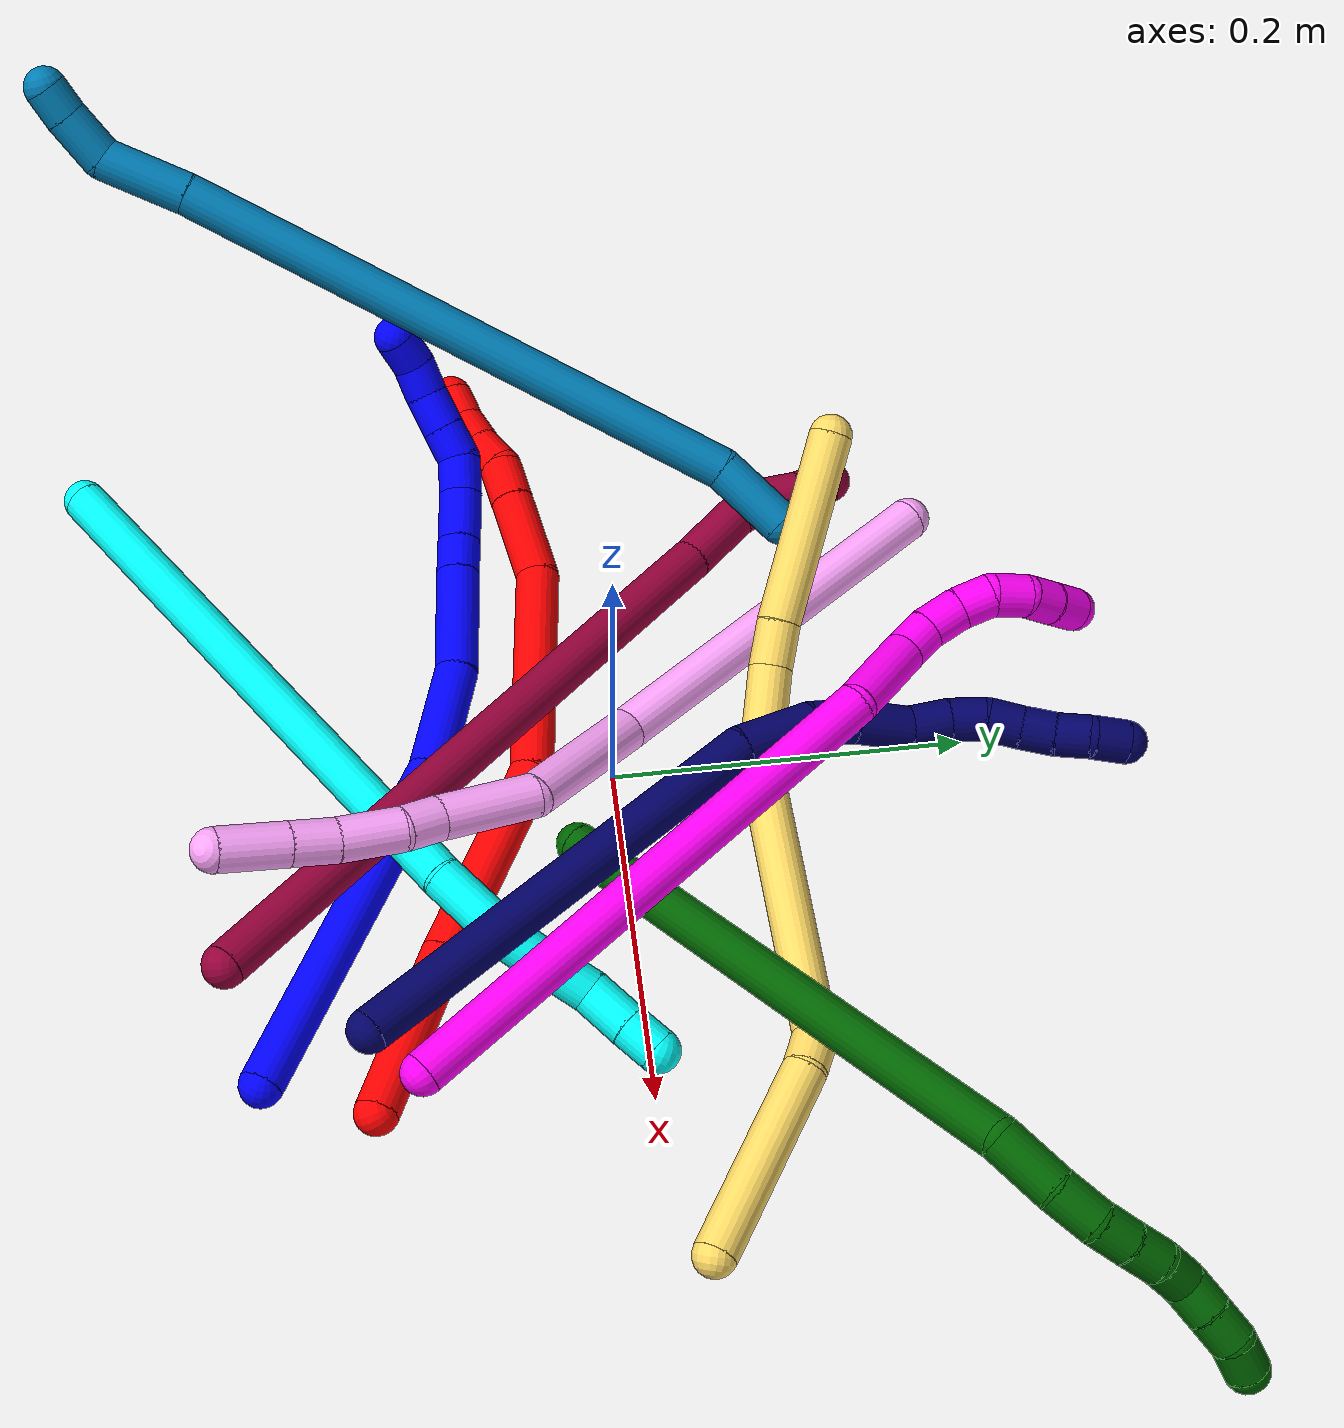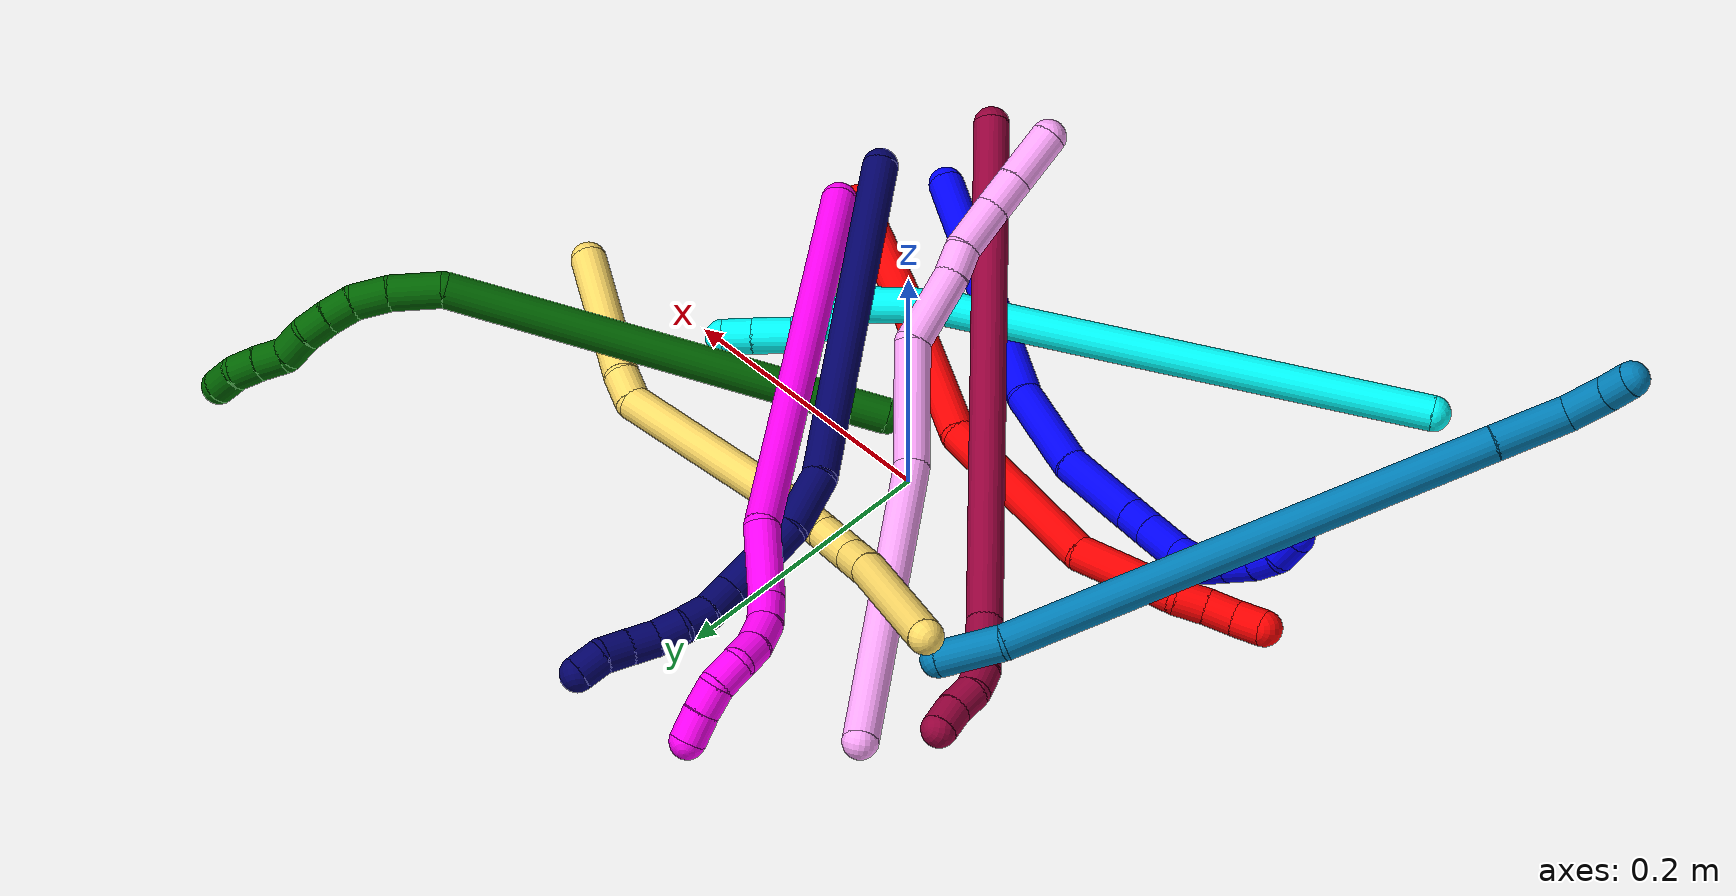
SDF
<sdf version="1.7">
 <world name="default">
  <plugin name="TubeGeneratorPlugin" filename="libtube_generator_plugin.so"/>
  <model name="photoneo_s_sensor">
   <static>1</static>
   <pose>0 0 2 1.57079 1.57079 3.14159</pose>
   <link name="link">
    <inertial><mass>0.1</mass></inertial>
    <sensor name="sensor" type="depth">
     <update_rate>30</update_rate>
     <camera>
      <horizontal_fov>1.22</horizontal_fov>
      <image><width>1920</width><height>1200</height><format>B8G8R8</format></image>
      <clip><near>0.1</near><far>2</far></clip>
      <depth_camera><output>points</output></depth_camera>
     </camera>
     <plugin name="camera_plugin" filename="libgazebo_ros_depth_camera.so">
      <baseline>0.2</baseline>
      <alwaysOn>1</alwaysOn>
      <updateRate>0.0</updateRate>
      <cameraName>camera_ir</cameraName>
      <imageTopicName>/camera/color/image_raw</imageTopicName>
      <cameraInfoTopicName>/camera/color/camera_info</cameraInfoTopicName>
      <depthImageTopicName>/camera/depth/image_raw</depthImageTopicName>
      <depthImageCameraInfoTopicName>/camera/depth/camera_info</depthImageCameraInfoTopicName>
      <pointCloudTopicName>/camera/depth/points</pointCloudTopicName>
      <frameName>fr_optical</frameName>
      <pointCloudCutoff>0.1</pointCloudCutoff>
      <pointCloudCutoffMax>2.0</pointCloudCutoffMax>
      <distortionK1>0</distortionK1>
      <distortionK2>0</distortionK2>
      <distortionK3>0</distortionK3>
      <distortionT1>0</distortionT1>
      <distortionT2>0</distortionT2>
      <CxPrime>0</CxPrime>
      <Cx>0</Cx>
      <Cy>0</Cy>
      <focalLength>0</focalLength>
      <hackBaseline>0</hackBaseline>
     </plugin>
    </sensor>
   </link>
  </model>
  <gravity>0 0 -9.8</gravity>
  <magnetic_field>6e-06 2.3e-05 -4.2e-05</magnetic_field>
  <atmosphere type="adiabatic"/>
  <physics name="default_physics" default="0" type="ode">
   <max_step_size>0.003</max_step_size>
   <real_time_factor>1</real_time_factor>
   <real_time_update_rate>1000</real_time_update_rate>
   <max_contacts>10000</max_contacts>
   <ode>
    <solver>
     <type>quick</type>
     <iters>100</iters>
     <sor>1.3</sor>
     <use_dynamic_moi_rescaling>0</use_dynamic_moi_rescaling>
    </solver>
    <constraints>
     <contact_max_correcting_vel>0</contact_max_correcting_vel>
     <contact_surface_layer>0.001</contact_surface_layer>
     <cfm>0</cfm>
     <erp>0.2</erp>
    </constraints>
   </ode>
  </physics>
  <scene><ambient>0.4 0.4 0.4 1</ambient><background>0.7 0.7 0.7 1</background><shadows>0</shadows></scene>
  <audio><device>default</device></audio>
  <spherical_coordinates>
   <surface_model>EARTH_WGS84</surface_model>
   <latitude_deg>0</latitude_deg>
   <longitude_deg>0</longitude_deg>
   <elevation>0</elevation>
   <heading_deg>0</heading_deg>
  </spherical_coordinates>
  <model name="bin">
   <static>1</static>
   <link name="bottom">
    <collision name="collision-bottom">
     <pose>0 0 -0.01 0 -0 0</pose>
     <geometry><box><size>0.8 0.6 0.02</size></box></geometry>
     <surface>
      <friction><ode><mu>100</mu><mu2>100</mu2></ode></friction>
      <contact><collide_bitmask>65535</collide_bitmask></contact>
     </surface>
    </collision>
   </link>
   <link name="west_wall">
    <collision name="collision-west_wall">
     <pose>-0.41 0 0.1 0 -0 0</pose>
     <geometry><box><size>0.02 0.6 0.2</size></box></geometry>
     <surface>
      <friction><ode><mu>100</mu><mu2>100</mu2></ode></friction>
      <contact><collide_bitmask>65535</collide_bitmask></contact>
     </surface>
    </collision>
   </link>
   <link name="east_wall">
    <collision name="collision-east_wall">
     <pose>0.41 0 0.1 0 -0 0</pose>
     <geometry><box><size>0.02 0.6 0.2</size></box></geometry>
     <surface>
      <friction><ode><mu>100</mu><mu2>100</mu2></ode></friction>
      <contact><collide_bitmask>65535</collide_bitmask></contact>
     </surface>
    </collision>
   </link>
   <link name="south_wall">
    <collision name="collision-south_wall">
     <pose>0 -0.31 0.1 0 -0 0</pose>
     <geometry><box><size>0.8 0.02 0.2</size></box></geometry>
     <surface>
      <friction><ode><mu>100</mu><mu2>100</mu2></ode></friction>
      <contact><collide_bitmask>65535</collide_bitmask></contact>
     </surface>
    </collision>
   </link>
   <link name="north_wall">
    <collision name="collision-north_wall">
     <pose>0 0.31 0.1 0 -0 0</pose>
     <geometry><box><size>0.8 0.02 0.2</size></box></geometry>
     <surface>
      <friction><ode><mu>100</mu><mu2>100</mu2></ode></friction>
      <contact><collide_bitmask>65535</collide_bitmask></contact>
     </surface>
    </collision>
   </link>
  </model>
  <model name="1">
   <static>0</static>
   <link name="1">
    <collision name="collision-cylinder-e_1_1_4">
     <pose>-0.084362 0.015062 -0.060694 -2.89834 -0.932909 2.66529</pose>
     <geometry><cylinder><radius>0.0125</radius><length>0.210024</length></cylinder></geometry>
     <surface>
      <friction><ode><mu>1.16</mu><mu2>1.16</mu2><slip1>0</slip1><slip2>0</slip2></ode></friction>
      <contact><ode><kp>1e+06</kp><kd>1</kd><max_vel>0</max_vel><min_depth>0.001</min_depth></ode></contact>
     </surface>
    </collision>
    <visual name="visual-cylinder-e_1_1_4">
     <pose>-0.084362 0.015062 -0.060694 -2.89834 -0.932909 2.66529</pose>
     <geometry><cylinder><radius>0.0125</radius><length>0.210024</length></cylinder></geometry>
     <material><ambient>0 0 1 1</ambient></material>
    </visual>
    <collision name="collision-cylinder-e_2_4_5">
     <pose>-0.19538 0.042397 -0.139062 -2.53465 -0.891665 1.98152</pose>
     <geometry><cylinder><radius>0.0125</radius><length>0.068515</length></cylinder></geometry>
     <surface>
      <friction><ode><mu>1.16</mu><mu2>1.16</mu2><slip1>0</slip1><slip2>0</slip2></ode></friction>
      <contact><ode><kp>1e+06</kp><kd>1</kd><max_vel>0</max_vel><min_depth>0.001</min_depth></ode></contact>
     </surface>
    </collision>
    <visual name="visual-cylinder-e_2_4_5">
     <pose>-0.19538 0.042397 -0.139062 -2.53465 -0.891665 1.98152</pose>
     <geometry><cylinder><radius>0.0125</radius><length>0.068515</length></cylinder></geometry>
     <material><ambient>0 0 1 1</ambient></material>
    </visual>
    <collision name="collision-cylinder-e_3_5_6">
     <pose>-0.24225 0.07164 -0.174721 -2.38523 -0.685294 1.46324</pose>
     <geometry><cylinder><radius>0.0125</radius><length>0.063876</length></cylinder></geometry>
     <surface>
      <friction><ode><mu>1.16</mu><mu2>1.16</mu2><slip1>0</slip1><slip2>0</slip2></ode></friction>
      <contact><ode><kp>1e+06</kp><kd>1</kd><max_vel>0</max_vel><min_depth>0.001</min_depth></ode></contact>
     </surface>
    </collision>
    <visual name="visual-cylinder-e_3_5_6">
     <pose>-0.24225 0.07164 -0.174721 -2.38523 -0.685294 1.46324</pose>
     <geometry><cylinder><radius>0.0125</radius><length>0.063876</length></cylinder></geometry>
     <material><ambient>0 0 1 1</ambient></material>
    </visual>
    <collision name="collision-cylinder-e_4_6_7">
     <pose>-0.268956 0.093913 -0.198757 -2.42196 -0.678934 1.5076</pose>
     <geometry><cylinder><radius>0.0125</radius><length>0.020676</length></cylinder></geometry>
     <surface>
      <friction><ode><mu>1.16</mu><mu2>1.16</mu2><slip1>0</slip1><slip2>0</slip2></ode></friction>
      <contact><ode><kp>1e+06</kp><kd>1</kd><max_vel>0</max_vel><min_depth>0.001</min_depth></ode></contact>
     </surface>
    </collision>
    <visual name="visual-cylinder-e_4_6_7">
     <pose>-0.268956 0.093913 -0.198757 -2.42196 -0.678934 1.5076</pose>
     <geometry><cylinder><radius>0.0125</radius><length>0.020676</length></cylinder></geometry>
     <material><ambient>0 0 1 1</ambient></material>
    </visual>
    <collision name="collision-cylinder-e_5_7_8">
     <pose>-0.285078 0.107232 -0.214224 -2.43633 -0.66168 1.50182</pose>
     <geometry><cylinder><radius>0.0125</radius><length>0.031347</length></cylinder></geometry>
     <surface>
      <friction><ode><mu>1.16</mu><mu2>1.16</mu2><slip1>0</slip1><slip2>0</slip2></ode></friction>
      <contact><ode><kp>1e+06</kp><kd>1</kd><max_vel>0</max_vel><min_depth>0.001</min_depth></ode></contact>
     </surface>
    </collision>
    <visual name="visual-cylinder-e_5_7_8">
     <pose>-0.285078 0.107232 -0.214224 -2.43633 -0.66168 1.50182</pose>
     <geometry><cylinder><radius>0.0125</radius><length>0.031347</length></cylinder></geometry>
     <material><ambient>0 0 1 1</ambient></material>
    </visual>
    <collision name="collision-cylinder-e_6_8_9">
     <pose>-0.299806 0.121178 -0.231607 -2.50182 -0.474132 1.26031</pose>
     <geometry><cylinder><radius>0.0125</radius><length>0.022327</length></cylinder></geometry>
     <surface>
      <friction><ode><mu>1.16</mu><mu2>1.16</mu2><slip1>0</slip1><slip2>0</slip2></ode></friction>
      <contact><ode><kp>1e+06</kp><kd>1</kd><max_vel>0</max_vel><min_depth>0.001</min_depth></ode></contact>
     </surface>
    </collision>
    <visual name="visual-cylinder-e_6_8_9">
     <pose>-0.299806 0.121178 -0.231607 -2.50182 -0.474132 1.26031</pose>
     <geometry><cylinder><radius>0.0125</radius><length>0.022327</length></cylinder></geometry>
     <material><ambient>0 0 1 1</ambient></material>
    </visual>
    <collision name="collision-cylinder-e_7_9_10">
     <pose>-0.305443 0.134836 -0.245994 -2.26389 -0.053766 0.11445</pose>
     <geometry><cylinder><radius>0.0125</radius><length>0.020123</length></cylinder></geometry>
     <surface>
      <friction><ode><mu>1.16</mu><mu2>1.16</mu2><slip1>0</slip1><slip2>0</slip2></ode></friction>
      <contact><ode><kp>1e+06</kp><kd>1</kd><max_vel>0</max_vel><min_depth>0.001</min_depth></ode></contact>
     </surface>
    </collision>
    <visual name="visual-cylinder-e_7_9_10">
     <pose>-0.305443 0.134836 -0.245994 -2.26389 -0.053766 0.11445</pose>
     <geometry><cylinder><radius>0.0125</radius><length>0.020123</length></cylinder></geometry>
     <material><ambient>0 0 1 1</ambient></material>
    </visual>
    <collision name="collision-cylinder-e_8_10_11">
     <pose>-0.306576 0.151105 -0.259564 -2.26784 -0.053085 0.113585</pose>
     <geometry><cylinder><radius>0.0125</radius><length>0.022309</length></cylinder></geometry>
     <surface>
      <friction><ode><mu>1.16</mu><mu2>1.16</mu2><slip1>0</slip1><slip2>0</slip2></ode></friction>
      <contact><ode><kp>1e+06</kp><kd>1</kd><max_vel>0</max_vel><min_depth>0.001</min_depth></ode></contact>
     </surface>
    </collision>
    <visual name="visual-cylinder-e_8_10_11">
     <pose>-0.306576 0.151105 -0.259564 -2.26784 -0.053085 0.113585</pose>
     <geometry><cylinder><radius>0.0125</radius><length>0.022309</length></cylinder></geometry>
     <material><ambient>0 0 1 1</ambient></material>
    </visual>
    <collision name="collision-cylinder-e_9_11_12">
     <pose>-0.306118 0.166018 -0.274537 -2.458 0.103707 -0.289725</pose>
     <geometry><cylinder><radius>0.0125</radius><length>0.020288</length></cylinder></geometry>
     <surface>
      <friction><ode><mu>1.16</mu><mu2>1.16</mu2><slip1>0</slip1><slip2>0</slip2></ode></friction>
      <contact><ode><kp>1e+06</kp><kd>1</kd><max_vel>0</max_vel><min_depth>0.001</min_depth></ode></contact>
     </surface>
    </collision>
    <visual name="visual-cylinder-e_9_11_12">
     <pose>-0.306118 0.166018 -0.274537 -2.458 0.103707 -0.289725</pose>
     <geometry><cylinder><radius>0.0125</radius><length>0.020288</length></cylinder></geometry>
     <material><ambient>0 0 1 1</ambient></material>
    </visual>
    <collision name="collision-cylinder-e_10_12_2">
     <pose>-0.300211 0.177845 -0.289563 -2.4935 0.493196 -1.28626</pose>
     <geometry><cylinder><radius>0.0125</radius><length>0.020515</length></cylinder></geometry>
     <surface>
      <friction><ode><mu>1.16</mu><mu2>1.16</mu2><slip1>0</slip1><slip2>0</slip2></ode></friction>
      <contact><ode><kp>1e+06</kp><kd>1</kd><max_vel>0</max_vel><min_depth>0.001</min_depth></ode></contact>
     </surface>
    </collision>
    <visual name="visual-cylinder-e_10_12_2">
     <pose>-0.300211 0.177845 -0.289563 -2.4935 0.493196 -1.28626</pose>
     <geometry><cylinder><radius>0.0125</radius><length>0.020515</length></cylinder></geometry>
     <material><ambient>0 0 1 1</ambient></material>
    </visual>
    <collision name="collision-sphere-2">
     <pose>-0.295355 0.183299 -0.296765 0 -0 0</pose>
     <geometry><sphere><radius>0.0125</radius></sphere></geometry>
     <surface>
      <friction><ode><mu>1.16</mu><mu2>1.16</mu2><slip1>0</slip1><slip2>0</slip2></ode></friction>
      <contact><ode><kp>1e+06</kp><kd>1</kd><max_vel>0</max_vel><min_depth>0.001</min_depth></ode></contact>
     </surface>
    </collision>
    <visual name="visual-sphere-2">
     <pose>-0.295355 0.183299 -0.296765 0 -0 0</pose>
     <geometry><sphere><radius>0.0125</radius></sphere></geometry>
     <material><ambient>0 0 1 1</ambient></material>
    </visual>
    <collision name="collision-sphere-12">
     <pose>-0.305068 0.172391 -0.28236 0 -0 0</pose>
     <geometry><sphere><radius>0.0125</radius></sphere></geometry>
     <surface>
      <friction><ode><mu>1.16</mu><mu2>1.16</mu2><slip1>0</slip1><slip2>0</slip2></ode></friction>
      <contact><ode><kp>1e+06</kp><kd>1</kd><max_vel>0</max_vel><min_depth>0.001</min_depth></ode></contact>
     </surface>
    </collision>
    <visual name="visual-sphere-12">
     <pose>-0.305068 0.172391 -0.28236 0 -0 0</pose>
     <geometry><sphere><radius>0.0125</radius></sphere></geometry>
     <material><ambient>0 0 1 1</ambient></material>
    </visual>
    <collision name="collision-sphere-11">
     <pose>-0.307168 0.159646 -0.266714 0 -0 0</pose>
     <geometry><sphere><radius>0.0125</radius></sphere></geometry>
     <surface>
      <friction><ode><mu>1.16</mu><mu2>1.16</mu2><slip1>0</slip1><slip2>0</slip2></ode></friction>
      <contact><ode><kp>1e+06</kp><kd>1</kd><max_vel>0</max_vel><min_depth>0.001</min_depth></ode></contact>
     </surface>
    </collision>
    <visual name="visual-sphere-11">
     <pose>-0.307168 0.159646 -0.266714 0 -0 0</pose>
     <geometry><sphere><radius>0.0125</radius></sphere></geometry>
     <material><ambient>0 0 1 1</ambient></material>
    </visual>
    <collision name="collision-sphere-10">
     <pose>-0.305984 0.142565 -0.252413 0 -0 0</pose>
     <geometry><sphere><radius>0.0125</radius></sphere></geometry>
     <surface>
      <friction><ode><mu>1.16</mu><mu2>1.16</mu2><slip1>0</slip1><slip2>0</slip2></ode></friction>
      <contact><ode><kp>1e+06</kp><kd>1</kd><max_vel>0</max_vel><min_depth>0.001</min_depth></ode></contact>
     </surface>
    </collision>
    <visual name="visual-sphere-10">
     <pose>-0.305984 0.142565 -0.252413 0 -0 0</pose>
     <geometry><sphere><radius>0.0125</radius></sphere></geometry>
     <material><ambient>0 0 1 1</ambient></material>
    </visual>
    <collision name="collision-sphere-9">
     <pose>-0.304903 0.127107 -0.239575 0 -0 0</pose>
     <geometry><sphere><radius>0.0125</radius></sphere></geometry>
     <surface>
      <friction><ode><mu>1.16</mu><mu2>1.16</mu2><slip1>0</slip1><slip2>0</slip2></ode></friction>
      <contact><ode><kp>1e+06</kp><kd>1</kd><max_vel>0</max_vel><min_depth>0.001</min_depth></ode></contact>
     </surface>
    </collision>
    <visual name="visual-sphere-9">
     <pose>-0.304903 0.127107 -0.239575 0 -0 0</pose>
     <geometry><sphere><radius>0.0125</radius></sphere></geometry>
     <material><ambient>0 0 1 1</ambient></material>
    </visual>
    <collision name="collision-sphere-4">
     <pose>-0.168724 0.030125 -0.121387 0 -0 0</pose>
     <geometry><sphere><radius>0.0125</radius></sphere></geometry>
     <surface>
      <friction><ode><mu>1.16</mu><mu2>1.16</mu2><slip1>0</slip1><slip2>0</slip2></ode></friction>
      <contact><ode><kp>1e+06</kp><kd>1</kd><max_vel>0</max_vel><min_depth>0.001</min_depth></ode></contact>
     </surface>
    </collision>
    <visual name="visual-sphere-4">
     <pose>-0.168724 0.030125 -0.121387 0 -0 0</pose>
     <geometry><sphere><radius>0.0125</radius></sphere></geometry>
     <material><ambient>0 0 1 1</ambient></material>
    </visual>
    <collision name="collision-sphere-1">
     <geometry><sphere><radius>0.0125</radius></sphere></geometry>
     <surface>
      <friction><ode><mu>1.16</mu><mu2>1.16</mu2><slip1>0</slip1><slip2>0</slip2></ode></friction>
      <contact><ode><kp>1e+06</kp><kd>1</kd><max_vel>0</max_vel><min_depth>0.001</min_depth></ode></contact>
     </surface>
    </collision>
    <visual name="visual-sphere-1">
     <geometry><sphere><radius>0.0125</radius></sphere></geometry>
     <material><ambient>0 0 1 1</ambient></material>
    </visual>
    <collision name="collision-sphere-8">
     <pose>-0.294709 0.115248 -0.223639 0 -0 0</pose>
     <geometry><sphere><radius>0.0125</radius></sphere></geometry>
     <surface>
      <friction><ode><mu>1.16</mu><mu2>1.16</mu2><slip1>0</slip1><slip2>0</slip2></ode></friction>
      <contact><ode><kp>1e+06</kp><kd>1</kd><max_vel>0</max_vel><min_depth>0.001</min_depth></ode></contact>
     </surface>
    </collision>
    <visual name="visual-sphere-8">
     <pose>-0.294709 0.115248 -0.223639 0 -0 0</pose>
     <geometry><sphere><radius>0.0125</radius></sphere></geometry>
     <material><ambient>0 0 1 1</ambient></material>
    </visual>
    <collision name="collision-sphere-5">
     <pose>-0.222037 0.05467 -0.156736 0 -0 0</pose>
     <geometry><sphere><radius>0.0125</radius></sphere></geometry>
     <surface>
      <friction><ode><mu>1.16</mu><mu2>1.16</mu2><slip1>0</slip1><slip2>0</slip2></ode></friction>
      <contact><ode><kp>1e+06</kp><kd>1</kd><max_vel>0</max_vel><min_depth>0.001</min_depth></ode></contact>
     </surface>
    </collision>
    <visual name="visual-sphere-5">
     <pose>-0.222037 0.05467 -0.156736 0 -0 0</pose>
     <geometry><sphere><radius>0.0125</radius></sphere></geometry>
     <material><ambient>0 0 1 1</ambient></material>
    </visual>
    <collision name="collision-sphere-6">
     <pose>-0.262464 0.08861 -0.192706 0 -0 0</pose>
     <geometry><sphere><radius>0.0125</radius></sphere></geometry>
     <surface>
      <friction><ode><mu>1.16</mu><mu2>1.16</mu2><slip1>0</slip1><slip2>0</slip2></ode></friction>
      <contact><ode><kp>1e+06</kp><kd>1</kd><max_vel>0</max_vel><min_depth>0.001</min_depth></ode></contact>
     </surface>
    </collision>
    <visual name="visual-sphere-6">
     <pose>-0.262464 0.08861 -0.192706 0 -0 0</pose>
     <geometry><sphere><radius>0.0125</radius></sphere></geometry>
     <material><ambient>0 0 1 1</ambient></material>
    </visual>
    <collision name="collision-sphere-7">
     <pose>-0.275448 0.099216 -0.204808 0 -0 0</pose>
     <geometry><sphere><radius>0.0125</radius></sphere></geometry>
     <surface>
      <friction><ode><mu>1.16</mu><mu2>1.16</mu2><slip1>0</slip1><slip2>0</slip2></ode></friction>
      <contact><ode><kp>1e+06</kp><kd>1</kd><max_vel>0</max_vel><min_depth>0.001</min_depth></ode></contact>
     </surface>
    </collision>
    <visual name="visual-sphere-7">
     <pose>-0.275448 0.099216 -0.204808 0 -0 0</pose>
     <geometry><sphere><radius>0.0125</radius></sphere></geometry>
     <material><ambient>0 0 1 1</ambient></material>
    </visual>
    <inertial>
     <pose>-0.186249 0.063508 -0.143364 0 -0 0</pose>
     <mass>0.5</mass>
     <inertia>
      <ixx>-0.000183</ixx>
      <ixy>0</ixy>
      <ixz>0</ixz>
      <iyy>0.001039</iyy>
      <iyz>0</iyz>
      <izz>0.000502</izz>
     </inertia>
    </inertial>
   </link>
   <pose>0.172231 -0.208647 0.011496 -3.08128 -0.603874 -0.710256</pose>
  </model>
  <model name="2">
   <static>0</static>
   <link name="2">
    <collision name="collision-cylinder-e_1_1_4">
     <pose>-0.042837 0.023736 0.015879 -0.981193 -0.982797 0.556891</pose>
     <geometry><cylinder><radius>0.0125</radius><length>0.102967</length></cylinder></geometry>
     <surface>
      <friction><ode><mu>1.16</mu><mu2>1.16</mu2><slip1>0</slip1><slip2>0</slip2></ode></friction>
      <contact><ode><kp>1e+06</kp><kd>1</kd><max_vel>0</max_vel><min_depth>0.001</min_depth></ode></contact>
     </surface>
    </collision>
    <visual name="visual-cylinder-e_1_1_4">
     <pose>-0.042837 0.023736 0.015879 -0.981193 -0.982797 0.556891</pose>
     <geometry><cylinder><radius>0.0125</radius><length>0.102967</length></cylinder></geometry>
     <material><ambient>1 0 0 1</ambient></material>
    </visual>
    <collision name="collision-cylinder-e_2_4_5">
     <pose>-0.135434 0.073661 0.056285 -0.818154 -0.946069 0.436682</pose>
     <geometry><cylinder><radius>0.0125</radius><length>0.122694</length></cylinder></geometry>
     <surface>
      <friction><ode><mu>1.16</mu><mu2>1.16</mu2><slip1>0</slip1><slip2>0</slip2></ode></friction>
      <contact><ode><kp>1e+06</kp><kd>1</kd><max_vel>0</max_vel><min_depth>0.001</min_depth></ode></contact>
     </surface>
    </collision>
    <visual name="visual-cylinder-e_2_4_5">
     <pose>-0.135434 0.073661 0.056285 -0.818154 -0.946069 0.436682</pose>
     <geometry><cylinder><radius>0.0125</radius><length>0.122694</length></cylinder></geometry>
     <material><ambient>1 0 0 1</ambient></material>
    </visual>
    <collision name="collision-cylinder-e_3_5_6">
     <pose>-0.248717 0.118681 0.086335 -1.28552 -1.27115 1.00939</pose>
     <geometry><cylinder><radius>0.0125</radius><length>0.132971</length></cylinder></geometry>
     <surface>
      <friction><ode><mu>1.16</mu><mu2>1.16</mu2><slip1>0</slip1><slip2>0</slip2></ode></friction>
      <contact><ode><kp>1e+06</kp><kd>1</kd><max_vel>0</max_vel><min_depth>0.001</min_depth></ode></contact>
     </surface>
    </collision>
    <visual name="visual-cylinder-e_3_5_6">
     <pose>-0.248717 0.118681 0.086335 -1.28552 -1.27115 1.00939</pose>
     <geometry><cylinder><radius>0.0125</radius><length>0.132971</length></cylinder></geometry>
     <material><ambient>1 0 0 1</ambient></material>
    </visual>
    <collision name="collision-cylinder-e_4_6_7">
     <pose>-0.338192 0.138426 0.088639 -2.86523 -1.44262 2.82791</pose>
     <geometry><cylinder><radius>0.0125</radius><length>0.052334</length></cylinder></geometry>
     <surface>
      <friction><ode><mu>1.16</mu><mu2>1.16</mu2><slip1>0</slip1><slip2>0</slip2></ode></friction>
      <contact><ode><kp>1e+06</kp><kd>1</kd><max_vel>0</max_vel><min_depth>0.001</min_depth></ode></contact>
     </surface>
    </collision>
    <visual name="visual-cylinder-e_4_6_7">
     <pose>-0.338192 0.138426 0.088639 -2.86523 -1.44262 2.82791</pose>
     <geometry><cylinder><radius>0.0125</radius><length>0.052334</length></cylinder></geometry>
     <material><ambient>1 0 0 1</ambient></material>
    </visual>
    <collision name="collision-cylinder-e_5_7_8">
     <pose>-0.376641 0.140117 0.083684 -2.72025 -1.41962 2.65373</pose>
     <geometry><cylinder><radius>0.0125</radius><length>0.025282</length></cylinder></geometry>
     <surface>
      <friction><ode><mu>1.16</mu><mu2>1.16</mu2><slip1>0</slip1><slip2>0</slip2></ode></friction>
      <contact><ode><kp>1e+06</kp><kd>1</kd><max_vel>0</max_vel><min_depth>0.001</min_depth></ode></contact>
     </surface>
    </collision>
    <visual name="visual-cylinder-e_5_7_8">
     <pose>-0.376641 0.140117 0.083684 -2.72025 -1.41962 2.65373</pose>
     <geometry><cylinder><radius>0.0125</radius><length>0.025282</length></cylinder></geometry>
     <material><ambient>1 0 0 1</ambient></material>
    </visual>
    <collision name="collision-cylinder-e_6_8_9">
     <pose>-0.398493 0.141271 0.076587 -3.07167 -1.04943 3.0209</pose>
     <geometry><cylinder><radius>0.0125</radius><length>0.021577</length></cylinder></geometry>
     <surface>
      <friction><ode><mu>1.16</mu><mu2>1.16</mu2><slip1>0</slip1><slip2>0</slip2></ode></friction>
      <contact><ode><kp>1e+06</kp><kd>1</kd><max_vel>0</max_vel><min_depth>0.001</min_depth></ode></contact>
     </surface>
    </collision>
    <visual name="visual-cylinder-e_6_8_9">
     <pose>-0.398493 0.141271 0.076587 -3.07167 -1.04943 3.0209</pose>
     <geometry><cylinder><radius>0.0125</radius><length>0.021577</length></cylinder></geometry>
     <material><ambient>1 0 0 1</ambient></material>
    </visual>
    <collision name="collision-cylinder-e_7_9_10">
     <pose>-0.417647 0.14251 0.067103 -2.93523 -1.16468 2.82966</pose>
     <geometry><cylinder><radius>0.0125</radius><length>0.021331</length></cylinder></geometry>
     <surface>
      <friction><ode><mu>1.16</mu><mu2>1.16</mu2><slip1>0</slip1><slip2>0</slip2></ode></friction>
      <contact><ode><kp>1e+06</kp><kd>1</kd><max_vel>0</max_vel><min_depth>0.001</min_depth></ode></contact>
     </surface>
    </collision>
    <visual name="visual-cylinder-e_7_9_10">
     <pose>-0.417647 0.14251 0.067103 -2.93523 -1.16468 2.82966</pose>
     <geometry><cylinder><radius>0.0125</radius><length>0.021331</length></cylinder></geometry>
     <material><ambient>1 0 0 1</ambient></material>
    </visual>
    <collision name="collision-cylinder-e_8_10_2">
     <pose>-0.437591 0.143283 0.060602 3.10383 -1.34051 -3.09395</pose>
     <geometry><cylinder><radius>0.0125</radius><length>0.020844</length></cylinder></geometry>
     <surface>
      <friction><ode><mu>1.16</mu><mu2>1.16</mu2><slip1>0</slip1><slip2>0</slip2></ode></friction>
      <contact><ode><kp>1e+06</kp><kd>1</kd><max_vel>0</max_vel><min_depth>0.001</min_depth></ode></contact>
     </surface>
    </collision>
    <visual name="visual-cylinder-e_8_10_2">
     <pose>-0.437591 0.143283 0.060602 3.10383 -1.34051 -3.09395</pose>
     <geometry><cylinder><radius>0.0125</radius><length>0.020844</length></cylinder></geometry>
     <material><ambient>1 0 0 1</ambient></material>
    </visual>
    <collision name="collision-sphere-2">
     <pose>-0.447738 0.143194 0.058224 0 -0 0</pose>
     <geometry><sphere><radius>0.0125</radius></sphere></geometry>
     <surface>
      <friction><ode><mu>1.16</mu><mu2>1.16</mu2><slip1>0</slip1><slip2>0</slip2></ode></friction>
      <contact><ode><kp>1e+06</kp><kd>1</kd><max_vel>0</max_vel><min_depth>0.001</min_depth></ode></contact>
     </surface>
    </collision>
    <visual name="visual-sphere-2">
     <pose>-0.447738 0.143194 0.058224 0 -0 0</pose>
     <geometry><sphere><radius>0.0125</radius></sphere></geometry>
     <material><ambient>1 0 0 1</ambient></material>
    </visual>
    <collision name="collision-sphere-10">
     <pose>-0.427444 0.143373 0.062979 0 -0 0</pose>
     <geometry><sphere><radius>0.0125</radius></sphere></geometry>
     <surface>
      <friction><ode><mu>1.16</mu><mu2>1.16</mu2><slip1>0</slip1><slip2>0</slip2></ode></friction>
      <contact><ode><kp>1e+06</kp><kd>1</kd><max_vel>0</max_vel><min_depth>0.001</min_depth></ode></contact>
     </surface>
    </collision>
    <visual name="visual-sphere-10">
     <pose>-0.427444 0.143373 0.062979 0 -0 0</pose>
     <geometry><sphere><radius>0.0125</radius></sphere></geometry>
     <material><ambient>1 0 0 1</ambient></material>
    </visual>
    <collision name="collision-sphere-9">
     <pose>-0.407849 0.141647 0.071227 0 -0 0</pose>
     <geometry><sphere><radius>0.0125</radius></sphere></geometry>
     <surface>
      <friction><ode><mu>1.16</mu><mu2>1.16</mu2><slip1>0</slip1><slip2>0</slip2></ode></friction>
      <contact><ode><kp>1e+06</kp><kd>1</kd><max_vel>0</max_vel><min_depth>0.001</min_depth></ode></contact>
     </surface>
    </collision>
    <visual name="visual-sphere-9">
     <pose>-0.407849 0.141647 0.071227 0 -0 0</pose>
     <geometry><sphere><radius>0.0125</radius></sphere></geometry>
     <material><ambient>1 0 0 1</ambient></material>
    </visual>
    <collision name="collision-sphere-4">
     <pose>-0.085674 0.047472 0.031758 0 -0 0</pose>
     <geometry><sphere><radius>0.0125</radius></sphere></geometry>
     <surface>
      <friction><ode><mu>1.16</mu><mu2>1.16</mu2><slip1>0</slip1><slip2>0</slip2></ode></friction>
      <contact><ode><kp>1e+06</kp><kd>1</kd><max_vel>0</max_vel><min_depth>0.001</min_depth></ode></contact>
     </surface>
    </collision>
    <visual name="visual-sphere-4">
     <pose>-0.085674 0.047472 0.031758 0 -0 0</pose>
     <geometry><sphere><radius>0.0125</radius></sphere></geometry>
     <material><ambient>1 0 0 1</ambient></material>
    </visual>
    <collision name="collision-sphere-1">
     <geometry><sphere><radius>0.0125</radius></sphere></geometry>
     <surface>
      <friction><ode><mu>1.16</mu><mu2>1.16</mu2><slip1>0</slip1><slip2>0</slip2></ode></friction>
      <contact><ode><kp>1e+06</kp><kd>1</kd><max_vel>0</max_vel><min_depth>0.001</min_depth></ode></contact>
     </surface>
    </collision>
    <visual name="visual-sphere-1">
     <geometry><sphere><radius>0.0125</radius></sphere></geometry>
     <material><ambient>1 0 0 1</ambient></material>
    </visual>
    <collision name="collision-sphere-8">
     <pose>-0.389138 0.140896 0.081947 0 -0 0</pose>
     <geometry><sphere><radius>0.0125</radius></sphere></geometry>
     <surface>
      <friction><ode><mu>1.16</mu><mu2>1.16</mu2><slip1>0</slip1><slip2>0</slip2></ode></friction>
      <contact><ode><kp>1e+06</kp><kd>1</kd><max_vel>0</max_vel><min_depth>0.001</min_depth></ode></contact>
     </surface>
    </collision>
    <visual name="visual-sphere-8">
     <pose>-0.389138 0.140896 0.081947 0 -0 0</pose>
     <geometry><sphere><radius>0.0125</radius></sphere></geometry>
     <material><ambient>1 0 0 1</ambient></material>
    </visual>
    <collision name="collision-sphere-5">
     <pose>-0.185194 0.09985 0.080812 0 -0 0</pose>
     <geometry><sphere><radius>0.0125</radius></sphere></geometry>
     <surface>
      <friction><ode><mu>1.16</mu><mu2>1.16</mu2><slip1>0</slip1><slip2>0</slip2></ode></friction>
      <contact><ode><kp>1e+06</kp><kd>1</kd><max_vel>0</max_vel><min_depth>0.001</min_depth></ode></contact>
     </surface>
    </collision>
    <visual name="visual-sphere-5">
     <pose>-0.185194 0.09985 0.080812 0 -0 0</pose>
     <geometry><sphere><radius>0.0125</radius></sphere></geometry>
     <material><ambient>1 0 0 1</ambient></material>
    </visual>
    <collision name="collision-sphere-6">
     <pose>-0.31224 0.137513 0.091857 0 -0 0</pose>
     <geometry><sphere><radius>0.0125</radius></sphere></geometry>
     <surface>
      <friction><ode><mu>1.16</mu><mu2>1.16</mu2><slip1>0</slip1><slip2>0</slip2></ode></friction>
      <contact><ode><kp>1e+06</kp><kd>1</kd><max_vel>0</max_vel><min_depth>0.001</min_depth></ode></contact>
     </surface>
    </collision>
    <visual name="visual-sphere-6">
     <pose>-0.31224 0.137513 0.091857 0 -0 0</pose>
     <geometry><sphere><radius>0.0125</radius></sphere></geometry>
     <material><ambient>1 0 0 1</ambient></material>
    </visual>
    <collision name="collision-sphere-7">
     <pose>-0.364145 0.139339 0.085422 0 -0 0</pose>
     <geometry><sphere><radius>0.0125</radius></sphere></geometry>
     <surface>
      <friction><ode><mu>1.16</mu><mu2>1.16</mu2><slip1>0</slip1><slip2>0</slip2></ode></friction>
      <contact><ode><kp>1e+06</kp><kd>1</kd><max_vel>0</max_vel><min_depth>0.001</min_depth></ode></contact>
     </surface>
    </collision>
    <visual name="visual-sphere-7">
     <pose>-0.364145 0.139339 0.085422 0 -0 0</pose>
     <geometry><sphere><radius>0.0125</radius></sphere></geometry>
     <material><ambient>1 0 0 1</ambient></material>
    </visual>
    <inertial>
     <pose>-0.215899 0.094249 0.062245 0 -0 0</pose>
     <mass>0.5</mass>
     <inertia>
      <ixx>0.00024</ixx>
      <ixy>0</ixy>
      <ixz>0</ixz>
      <iyy>0.000555</iyy>
      <iyz>0</iyz>
      <izz>0.000256</izz>
     </inertia>
    </inertial>
   </link>
   <pose>0.19857 -0.148674 0.018595 -0.985043 0.179023 0.09881</pose>
  </model>
  <model name="3">
   <static>0</static>
   <link name="3">
    <collision name="collision-cylinder-e_1_1_4">
     <pose>0.152517 0.071195 -0.040633 -2.08942 1.07762 -1.59988</pose>
     <geometry><cylinder><radius>0.0125</radius><length>0.346302</length></cylinder></geometry>
     <surface>
      <friction><ode><mu>1.16</mu><mu2>1.16</mu2><slip1>0</slip1><slip2>0</slip2></ode></friction>
      <contact><ode><kp>1e+06</kp><kd>1</kd><max_vel>0</max_vel><min_depth>0.001</min_depth></ode></contact>
     </surface>
    </collision>
    <visual name="visual-cylinder-e_1_1_4">
     <pose>0.152517 0.071195 -0.040633 -2.08942 1.07762 -1.59988</pose>
     <geometry><cylinder><radius>0.0125</radius><length>0.346302</length></cylinder></geometry>
     <material><ambient>0.003922 1 0.996078 1</ambient></material>
    </visual>
    <collision name="collision-cylinder-e_2_4_5">
     <pose>0.32554 0.157332 -0.087364 -1.95821 0.90403 -1.25137</pose>
     <geometry><cylinder><radius>0.0125</radius><length>0.05219</length></cylinder></geometry>
     <surface>
      <friction><ode><mu>1.16</mu><mu2>1.16</mu2><slip1>0</slip1><slip2>0</slip2></ode></friction>
      <contact><ode><kp>1e+06</kp><kd>1</kd><max_vel>0</max_vel><min_depth>0.001</min_depth></ode></contact>
     </surface>
    </collision>
    <visual name="visual-cylinder-e_2_4_5">
     <pose>0.32554 0.157332 -0.087364 -1.95821 0.90403 -1.25137</pose>
     <geometry><cylinder><radius>0.0125</radius><length>0.05219</length></cylinder></geometry>
     <material><ambient>0.003922 1 0.996078 1</ambient></material>
    </visual>
    <collision name="collision-cylinder-e_3_5_6">
     <pose>0.358086 0.194889 -0.097292 -1.73863 0.483377 -0.567807</pose>
     <geometry><cylinder><radius>0.0125</radius><length>0.051809</length></cylinder></geometry>
     <surface>
      <friction><ode><mu>1.16</mu><mu2>1.16</mu2><slip1>0</slip1><slip2>0</slip2></ode></friction>
      <contact><ode><kp>1e+06</kp><kd>1</kd><max_vel>0</max_vel><min_depth>0.001</min_depth></ode></contact>
     </surface>
    </collision>
    <visual name="visual-cylinder-e_3_5_6">
     <pose>0.358086 0.194889 -0.097292 -1.73863 0.483377 -0.567807</pose>
     <geometry><cylinder><radius>0.0125</radius><length>0.051809</length></cylinder></geometry>
     <material><ambient>0.003922 1 0.996078 1</ambient></material>
    </visual>
    <collision name="collision-cylinder-e_4_6_7">
     <pose>0.381224 0.226246 -0.104326 -1.92193 0.872752 -1.17716</pose>
     <geometry><cylinder><radius>0.0125</radius><length>0.028974</length></cylinder></geometry>
     <surface>
      <friction><ode><mu>1.16</mu><mu2>1.16</mu2><slip1>0</slip1><slip2>0</slip2></ode></friction>
      <contact><ode><kp>1e+06</kp><kd>1</kd><max_vel>0</max_vel><min_depth>0.001</min_depth></ode></contact>
     </surface>
    </collision>
    <visual name="visual-cylinder-e_4_6_7">
     <pose>0.381224 0.226246 -0.104326 -1.92193 0.872752 -1.17716</pose>
     <geometry><cylinder><radius>0.0125</radius><length>0.028974</length></cylinder></geometry>
     <material><ambient>0.003922 1 0.996078 1</ambient></material>
    </visual>
    <collision name="collision-cylinder-e_5_7_2">
     <pose>0.400143 0.241468 -0.109592 -1.87903 0.855143 -1.11476</pose>
     <geometry><cylinder><radius>0.0125</radius><length>0.020725</length></cylinder></geometry>
     <surface>
      <friction><ode><mu>1.16</mu><mu2>1.16</mu2><slip1>0</slip1><slip2>0</slip2></ode></friction>
      <contact><ode><kp>1e+06</kp><kd>1</kd><max_vel>0</max_vel><min_depth>0.001</min_depth></ode></contact>
     </surface>
    </collision>
    <visual name="visual-cylinder-e_5_7_2">
     <pose>0.400143 0.241468 -0.109592 -1.87903 0.855143 -1.11476</pose>
     <geometry><cylinder><radius>0.0125</radius><length>0.020725</length></cylinder></geometry>
     <material><ambient>0.003922 1 0.996078 1</ambient></material>
    </visual>
    <collision name="collision-sphere-2">
     <pose>0.407963 0.247947 -0.111654 0 -0 0</pose>
     <geometry><sphere><radius>0.0125</radius></sphere></geometry>
     <surface>
      <friction><ode><mu>1.16</mu><mu2>1.16</mu2><slip1>0</slip1><slip2>0</slip2></ode></friction>
      <contact><ode><kp>1e+06</kp><kd>1</kd><max_vel>0</max_vel><min_depth>0.001</min_depth></ode></contact>
     </surface>
    </collision>
    <visual name="visual-sphere-2">
     <pose>0.407963 0.247947 -0.111654 0 -0 0</pose>
     <geometry><sphere><radius>0.0125</radius></sphere></geometry>
     <material><ambient>0.003922 1 0.996078 1</ambient></material>
    </visual>
    <collision name="collision-sphere-7">
     <pose>0.392322 0.234989 -0.107529 0 -0 0</pose>
     <geometry><sphere><radius>0.0125</radius></sphere></geometry>
     <surface>
      <friction><ode><mu>1.16</mu><mu2>1.16</mu2><slip1>0</slip1><slip2>0</slip2></ode></friction>
      <contact><ode><kp>1e+06</kp><kd>1</kd><max_vel>0</max_vel><min_depth>0.001</min_depth></ode></contact>
     </surface>
    </collision>
    <visual name="visual-sphere-7">
     <pose>0.392322 0.234989 -0.107529 0 -0 0</pose>
     <geometry><sphere><radius>0.0125</radius></sphere></geometry>
     <material><ambient>0.003922 1 0.996078 1</ambient></material>
    </visual>
    <collision name="collision-sphere-6">
     <pose>0.370126 0.217503 -0.101124 0 -0 0</pose>
     <geometry><sphere><radius>0.0125</radius></sphere></geometry>
     <surface>
      <friction><ode><mu>1.16</mu><mu2>1.16</mu2><slip1>0</slip1><slip2>0</slip2></ode></friction>
      <contact><ode><kp>1e+06</kp><kd>1</kd><max_vel>0</max_vel><min_depth>0.001</min_depth></ode></contact>
     </surface>
    </collision>
    <visual name="visual-sphere-6">
     <pose>0.370126 0.217503 -0.101124 0 -0 0</pose>
     <geometry><sphere><radius>0.0125</radius></sphere></geometry>
     <material><ambient>0.003922 1 0.996078 1</ambient></material>
    </visual>
    <collision name="collision-sphere-5">
     <pose>0.346046 0.172275 -0.093461 0 -0 0</pose>
     <geometry><sphere><radius>0.0125</radius></sphere></geometry>
     <surface>
      <friction><ode><mu>1.16</mu><mu2>1.16</mu2><slip1>0</slip1><slip2>0</slip2></ode></friction>
      <contact><ode><kp>1e+06</kp><kd>1</kd><max_vel>0</max_vel><min_depth>0.001</min_depth></ode></contact>
     </surface>
    </collision>
    <visual name="visual-sphere-5">
     <pose>0.346046 0.172275 -0.093461 0 -0 0</pose>
     <geometry><sphere><radius>0.0125</radius></sphere></geometry>
     <material><ambient>0.003922 1 0.996078 1</ambient></material>
    </visual>
    <collision name="collision-sphere-1">
     <geometry><sphere><radius>0.0125</radius></sphere></geometry>
     <surface>
      <friction><ode><mu>1.16</mu><mu2>1.16</mu2><slip1>0</slip1><slip2>0</slip2></ode></friction>
      <contact><ode><kp>1e+06</kp><kd>1</kd><max_vel>0</max_vel><min_depth>0.001</min_depth></ode></contact>
     </surface>
    </collision>
    <visual name="visual-sphere-1">
     <geometry><sphere><radius>0.0125</radius></sphere></geometry>
     <material><ambient>0.003922 1 0.996078 1</ambient></material>
    </visual>
    <collision name="collision-sphere-4">
     <pose>0.305034 0.14239 -0.081267 0 -0 0</pose>
     <geometry><sphere><radius>0.0125</radius></sphere></geometry>
     <surface>
      <friction><ode><mu>1.16</mu><mu2>1.16</mu2><slip1>0</slip1><slip2>0</slip2></ode></friction>
      <contact><ode><kp>1e+06</kp><kd>1</kd><max_vel>0</max_vel><min_depth>0.001</min_depth></ode></contact>
     </surface>
    </collision>
    <visual name="visual-sphere-4">
     <pose>0.305034 0.14239 -0.081267 0 -0 0</pose>
     <geometry><sphere><radius>0.0125</radius></sphere></geometry>
     <material><ambient>0.003922 1 0.996078 1</ambient></material>
    </visual>
    <inertial>
     <pose>0.215395 0.109046 -0.057931 0 -0 0</pose>
     <mass>0.5</mass>
     <inertia>
      <ixx>-0.001663</ixx>
      <ixy>0</ixy>
      <ixz>0</ixz>
      <iyy>0.001077</iyy>
      <iyz>0</iyz>
      <izz>-0.004541</izz>
     </inertia>
    </inertial>
   </link>
   <pose>-0.216283 -0.288501 0.013354 -0.851539 -0.565841 0.476503</pose>
  </model>
  <model name="4">
   <static>0</static>
   <link name="4">
    <collision name="collision-cylinder-e_1_1_4">
     <pose>0.027207 -0.07996 -0.07725 2.33896 0.239992 0.553694</pose>
     <geometry><cylinder><radius>0.0125</radius><length>0.228923</length></cylinder></geometry>
     <surface>
      <friction><ode><mu>1.16</mu><mu2>1.16</mu2><slip1>0</slip1><slip2>0</slip2></ode></friction>
      <contact><ode><kp>1e+06</kp><kd>1</kd><max_vel>0</max_vel><min_depth>0.001</min_depth></ode></contact>
     </surface>
    </collision>
    <visual name="visual-cylinder-e_1_1_4">
     <pose>0.027207 -0.07996 -0.07725 2.33896 0.239992 0.553694</pose>
     <geometry><cylinder><radius>0.0125</radius><length>0.228923</length></cylinder></geometry>
     <material><ambient>1 0.65098 0.996078 1</ambient></material>
    </visual>
    <collision name="collision-cylinder-e_2_4_5">
     <pose>0.054866 -0.182045 -0.192675 2.61633 0.010249 0.038118</pose>
     <geometry><cylinder><radius>0.0125</radius><length>0.088249</length></cylinder></geometry>
     <surface>
      <friction><ode><mu>1.16</mu><mu2>1.16</mu2><slip1>0</slip1><slip2>0</slip2></ode></friction>
      <contact><ode><kp>1e+06</kp><kd>1</kd><max_vel>0</max_vel><min_depth>0.001</min_depth></ode></contact>
     </surface>
    </collision>
    <visual name="visual-cylinder-e_2_4_5">
     <pose>0.054866 -0.182045 -0.192675 2.61633 0.010249 0.038118</pose>
     <geometry><cylinder><radius>0.0125</radius><length>0.088249</length></cylinder></geometry>
     <material><ambient>1 0.65098 0.996078 1</ambient></material>
    </visual>
    <collision name="collision-cylinder-e_3_5_6">
     <pose>0.069196 -0.216458 -0.252445 2.62424 0.509358 1.55452</pose>
     <geometry><cylinder><radius>0.0125</radius><length>0.05692</length></cylinder></geometry>
     <surface>
      <friction><ode><mu>1.16</mu><mu2>1.16</mu2><slip1>0</slip1><slip2>0</slip2></ode></friction>
      <contact><ode><kp>1e+06</kp><kd>1</kd><max_vel>0</max_vel><min_depth>0.001</min_depth></ode></contact>
     </surface>
    </collision>
    <visual name="visual-cylinder-e_3_5_6">
     <pose>0.069196 -0.216458 -0.252445 2.62424 0.509358 1.55452</pose>
     <geometry><cylinder><radius>0.0125</radius><length>0.05692</length></cylinder></geometry>
     <material><ambient>1 0.65098 0.996078 1</ambient></material>
    </visual>
    <collision name="collision-cylinder-e_4_6_7">
     <pose>0.086972 -0.233566 -0.283344 2.66375 0.356252 1.27302</pose>
     <geometry><cylinder><radius>0.0125</radius><length>0.022359</length></cylinder></geometry>
     <surface>
      <friction><ode><mu>1.16</mu><mu2>1.16</mu2><slip1>0</slip1><slip2>0</slip2></ode></friction>
      <contact><ode><kp>1e+06</kp><kd>1</kd><max_vel>0</max_vel><min_depth>0.001</min_depth></ode></contact>
     </surface>
    </collision>
    <visual name="visual-cylinder-e_4_6_7">
     <pose>0.086972 -0.233566 -0.283344 2.66375 0.356252 1.27302</pose>
     <geometry><cylinder><radius>0.0125</radius><length>0.022359</length></cylinder></geometry>
     <material><ambient>1 0.65098 0.996078 1</ambient></material>
    </visual>
    <collision name="collision-cylinder-e_5_7_8">
     <pose>0.10137 -0.245706 -0.305769 2.6326 0.609876 1.76024</pose>
     <geometry><cylinder><radius>0.0125</radius><length>0.036661</length></cylinder></geometry>
     <surface>
      <friction><ode><mu>1.16</mu><mu2>1.16</mu2><slip1>0</slip1><slip2>0</slip2></ode></friction>
      <contact><ode><kp>1e+06</kp><kd>1</kd><max_vel>0</max_vel><min_depth>0.001</min_depth></ode></contact>
     </surface>
    </collision>
    <visual name="visual-cylinder-e_5_7_8">
     <pose>0.10137 -0.245706 -0.305769 2.6326 0.609876 1.76024</pose>
     <geometry><cylinder><radius>0.0125</radius><length>0.036661</length></cylinder></geometry>
     <material><ambient>1 0.65098 0.996078 1</ambient></material>
    </visual>
    <collision name="collision-cylinder-e_6_8_9">
     <pose>0.119527 -0.257112 -0.328953 2.75611 0.614139 2.03817</pose>
     <geometry><cylinder><radius>0.0125</radius><length>0.026576</length></cylinder></geometry>
     <surface>
      <friction><ode><mu>1.16</mu><mu2>1.16</mu2><slip1>0</slip1><slip2>0</slip2></ode></friction>
      <contact><ode><kp>1e+06</kp><kd>1</kd><max_vel>0</max_vel><min_depth>0.001</min_depth></ode></contact>
     </surface>
    </collision>
    <visual name="visual-cylinder-e_6_8_9">
     <pose>0.119527 -0.257112 -0.328953 2.75611 0.614139 2.03817</pose>
     <geometry><cylinder><radius>0.0125</radius><length>0.026576</length></cylinder></geometry>
     <material><ambient>1 0.65098 0.996078 1</ambient></material>
    </visual>
    <collision name="collision-cylinder-e_7_9_2">
     <pose>0.138822 -0.267394 -0.354261 2.75536 0.615512 2.0385</pose>
     <geometry><cylinder><radius>0.0125</radius><length>0.040312</length></cylinder></geometry>
     <surface>
      <friction><ode><mu>1.16</mu><mu2>1.16</mu2><slip1>0</slip1><slip2>0</slip2></ode></friction>
      <contact><ode><kp>1e+06</kp><kd>1</kd><max_vel>0</max_vel><min_depth>0.001</min_depth></ode></contact>
     </surface>
    </collision>
    <visual name="visual-cylinder-e_7_9_2">
     <pose>0.138822 -0.267394 -0.354261 2.75536 0.615512 2.0385</pose>
     <geometry><cylinder><radius>0.0125</radius><length>0.040312</length></cylinder></geometry>
     <material><ambient>1 0.65098 0.996078 1</ambient></material>
    </visual>
    <collision name="collision-sphere-2">
     <pose>0.150459 -0.273594 -0.369505 0 -0 0</pose>
     <geometry><sphere><radius>0.0125</radius></sphere></geometry>
     <surface>
      <friction><ode><mu>1.16</mu><mu2>1.16</mu2><slip1>0</slip1><slip2>0</slip2></ode></friction>
      <contact><ode><kp>1e+06</kp><kd>1</kd><max_vel>0</max_vel><min_depth>0.001</min_depth></ode></contact>
     </surface>
    </collision>
    <visual name="visual-sphere-2">
     <pose>0.150459 -0.273594 -0.369505 0 -0 0</pose>
     <geometry><sphere><radius>0.0125</radius></sphere></geometry>
     <material><ambient>1 0.65098 0.996078 1</ambient></material>
    </visual>
    <collision name="collision-sphere-9">
     <pose>0.127184 -0.261195 -0.339016 0 -0 0</pose>
     <geometry><sphere><radius>0.0125</radius></sphere></geometry>
     <surface>
      <friction><ode><mu>1.16</mu><mu2>1.16</mu2><slip1>0</slip1><slip2>0</slip2></ode></friction>
      <contact><ode><kp>1e+06</kp><kd>1</kd><max_vel>0</max_vel><min_depth>0.001</min_depth></ode></contact>
     </surface>
    </collision>
    <visual name="visual-sphere-9">
     <pose>0.127184 -0.261195 -0.339016 0 -0 0</pose>
     <geometry><sphere><radius>0.0125</radius></sphere></geometry>
     <material><ambient>1 0.65098 0.996078 1</ambient></material>
    </visual>
    <collision name="collision-sphere-4">
     <pose>0.054414 -0.15992 -0.154501 0 -0 0</pose>
     <geometry><sphere><radius>0.0125</radius></sphere></geometry>
     <surface>
      <friction><ode><mu>1.16</mu><mu2>1.16</mu2><slip1>0</slip1><slip2>0</slip2></ode></friction>
      <contact><ode><kp>1e+06</kp><kd>1</kd><max_vel>0</max_vel><min_depth>0.001</min_depth></ode></contact>
     </surface>
    </collision>
    <visual name="visual-sphere-4">
     <pose>0.054414 -0.15992 -0.154501 0 -0 0</pose>
     <geometry><sphere><radius>0.0125</radius></sphere></geometry>
     <material><ambient>1 0.65098 0.996078 1</ambient></material>
    </visual>
    <collision name="collision-sphere-1">
     <geometry><sphere><radius>0.0125</radius></sphere></geometry>
     <surface>
      <friction><ode><mu>1.16</mu><mu2>1.16</mu2><slip1>0</slip1><slip2>0</slip2></ode></friction>
      <contact><ode><kp>1e+06</kp><kd>1</kd><max_vel>0</max_vel><min_depth>0.001</min_depth></ode></contact>
     </surface>
    </collision>
    <visual name="visual-sphere-1">
     <geometry><sphere><radius>0.0125</radius></sphere></geometry>
     <material><ambient>1 0.65098 0.996078 1</ambient></material>
    </visual>
    <collision name="collision-sphere-8">
     <pose>0.11187 -0.253028 -0.31889 0 -0 0</pose>
     <geometry><sphere><radius>0.0125</radius></sphere></geometry>
     <surface>
      <friction><ode><mu>1.16</mu><mu2>1.16</mu2><slip1>0</slip1><slip2>0</slip2></ode></friction>
      <contact><ode><kp>1e+06</kp><kd>1</kd><max_vel>0</max_vel><min_depth>0.001</min_depth></ode></contact>
     </surface>
    </collision>
    <visual name="visual-sphere-8">
     <pose>0.11187 -0.253028 -0.31889 0 -0 0</pose>
     <geometry><sphere><radius>0.0125</radius></sphere></geometry>
     <material><ambient>1 0.65098 0.996078 1</ambient></material>
    </visual>
    <collision name="collision-sphere-5">
     <pose>0.055318 -0.204169 -0.230849 0 -0 0</pose>
     <geometry><sphere><radius>0.0125</radius></sphere></geometry>
     <surface>
      <friction><ode><mu>1.16</mu><mu2>1.16</mu2><slip1>0</slip1><slip2>0</slip2></ode></friction>
      <contact><ode><kp>1e+06</kp><kd>1</kd><max_vel>0</max_vel><min_depth>0.001</min_depth></ode></contact>
     </surface>
    </collision>
    <visual name="visual-sphere-5">
     <pose>0.055318 -0.204169 -0.230849 0 -0 0</pose>
     <geometry><sphere><radius>0.0125</radius></sphere></geometry>
     <material><ambient>1 0.65098 0.996078 1</ambient></material>
    </visual>
    <collision name="collision-sphere-6">
     <pose>0.083073 -0.228747 -0.27404 0 -0 0</pose>
     <geometry><sphere><radius>0.0125</radius></sphere></geometry>
     <surface>
      <friction><ode><mu>1.16</mu><mu2>1.16</mu2><slip1>0</slip1><slip2>0</slip2></ode></friction>
      <contact><ode><kp>1e+06</kp><kd>1</kd><max_vel>0</max_vel><min_depth>0.001</min_depth></ode></contact>
     </surface>
    </collision>
    <visual name="visual-sphere-6">
     <pose>0.083073 -0.228747 -0.27404 0 -0 0</pose>
     <geometry><sphere><radius>0.0125</radius></sphere></geometry>
     <material><ambient>1 0.65098 0.996078 1</ambient></material>
    </visual>
    <collision name="collision-sphere-7">
     <pose>0.090871 -0.238384 -0.292648 0 -0 0</pose>
     <geometry><sphere><radius>0.0125</radius></sphere></geometry>
     <surface>
      <friction><ode><mu>1.16</mu><mu2>1.16</mu2><slip1>0</slip1><slip2>0</slip2></ode></friction>
      <contact><ode><kp>1e+06</kp><kd>1</kd><max_vel>0</max_vel><min_depth>0.001</min_depth></ode></contact>
     </surface>
    </collision>
    <visual name="visual-sphere-7">
     <pose>0.090871 -0.238384 -0.292648 0 -0 0</pose>
     <geometry><sphere><radius>0.0125</radius></sphere></geometry>
     <material><ambient>1 0.65098 0.996078 1</ambient></material>
    </visual>
    <inertial>
     <pose>0.058885 -0.157066 -0.17925 0 -0 0</pose>
     <mass>0.5</mass>
     <inertia>
      <ixx>0.001448</ixx>
      <ixy>0</ixy>
      <ixz>0</ixz>
      <iyy>-2.1e-05</iyy>
      <iyz>0</iyz>
      <izz>0.000461</izz>
     </inertia>
    </inertial>
   </link>
   <pose>-0.147749 0.19283 0.012427 2.53328 0.263541 -2.2297</pose>
  </model>
  <model name="5">
   <static>0</static>
   <link name="5">
    <collision name="collision-cylinder-e_1_1_4">
     <pose>-0.008868 -0.002865 0.055325 0.051746 -0.158736 -0.004117</pose>
     <geometry><cylinder><radius>0.0125</radius><length>0.112209</length></cylinder></geometry>
     <surface>
      <friction><ode><mu>1.16</mu><mu2>1.16</mu2><slip1>0</slip1><slip2>0</slip2></ode></friction>
      <contact><ode><kp>1e+06</kp><kd>1</kd><max_vel>0</max_vel><min_depth>0.001</min_depth></ode></contact>
     </surface>
    </collision>
    <visual name="visual-cylinder-e_1_1_4">
     <pose>-0.008868 -0.002865 0.055325 0.051746 -0.158736 -0.004117</pose>
     <geometry><cylinder><radius>0.0125</radius><length>0.112209</length></cylinder></geometry>
     <material><ambient>1 0.858824 0.4 1</ambient></material>
    </visual>
    <collision name="collision-cylinder-e_2_4_5">
     <pose>-0.018724 -0.005896 0.123958 0.012412 -0.074029 -0.00046</pose>
     <geometry><cylinder><radius>0.0125</radius><length>0.026692</length></cylinder></geometry>
     <surface>
      <friction><ode><mu>1.16</mu><mu2>1.16</mu2><slip1>0</slip1><slip2>0</slip2></ode></friction>
      <contact><ode><kp>1e+06</kp><kd>1</kd><max_vel>0</max_vel><min_depth>0.001</min_depth></ode></contact>
     </surface>
    </collision>
    <visual name="visual-cylinder-e_2_4_5">
     <pose>-0.018724 -0.005896 0.123958 0.012412 -0.074029 -0.00046</pose>
     <geometry><cylinder><radius>0.0125</radius><length>0.026692</length></cylinder></geometry>
     <material><ambient>1 0.858824 0.4 1</ambient></material>
    </visual>
    <collision name="collision-cylinder-e_3_5_6">
     <pose>-0.021968 -0.003405 0.156272 -0.138878 -0.117092 0.008153</pose>
     <geometry><cylinder><radius>0.0125</radius><length>0.038644</length></cylinder></geometry>
     <surface>
      <friction><ode><mu>1.16</mu><mu2>1.16</mu2><slip1>0</slip1><slip2>0</slip2></ode></friction>
      <contact><ode><kp>1e+06</kp><kd>1</kd><max_vel>0</max_vel><min_depth>0.001</min_depth></ode></contact>
     </surface>
    </collision>
    <visual name="visual-cylinder-e_3_5_6">
     <pose>-0.021968 -0.003405 0.156272 -0.138878 -0.117092 0.008153</pose>
     <geometry><cylinder><radius>0.0125</radius><length>0.038644</length></cylinder></geometry>
     <material><ambient>1 0.858824 0.4 1</ambient></material>
    </visual>
    <collision name="collision-cylinder-e_4_6_7">
     <pose>-0.027115 0.006275 0.192315 -0.391013 -0.155534 0.030861</pose>
     <geometry><cylinder><radius>0.0125</radius><length>0.037308</length></cylinder></geometry>
     <surface>
      <friction><ode><mu>1.16</mu><mu2>1.16</mu2><slip1>0</slip1><slip2>0</slip2></ode></friction>
      <contact><ode><kp>1e+06</kp><kd>1</kd><max_vel>0</max_vel><min_depth>0.001</min_depth></ode></contact>
     </surface>
    </collision>
    <visual name="visual-cylinder-e_4_6_7">
     <pose>-0.027115 0.006275 0.192315 -0.391013 -0.155534 0.030861</pose>
     <geometry><cylinder><radius>0.0125</radius><length>0.037308</length></cylinder></geometry>
     <material><ambient>1 0.858824 0.4 1</ambient></material>
    </visual>
    <collision name="collision-cylinder-e_5_7_8">
     <pose>-0.036371 0.049581 0.273132 -0.517214 -0.08654 0.022906</pose>
     <geometry><cylinder><radius>0.0125</radius><length>0.147304</length></cylinder></geometry>
     <surface>
      <friction><ode><mu>1.16</mu><mu2>1.16</mu2><slip1>0</slip1><slip2>0</slip2></ode></friction>
      <contact><ode><kp>1e+06</kp><kd>1</kd><max_vel>0</max_vel><min_depth>0.001</min_depth></ode></contact>
     </surface>
    </collision>
    <visual name="visual-cylinder-e_5_7_8">
     <pose>-0.036371 0.049581 0.273132 -0.517214 -0.08654 0.022906</pose>
     <geometry><cylinder><radius>0.0125</radius><length>0.147304</length></cylinder></geometry>
     <material><ambient>1 0.858824 0.4 1</ambient></material>
    </visual>
    <collision name="collision-cylinder-e_6_8_9">
     <pose>-0.04881 0.089289 0.345944 -0.362541 -0.561181 0.105544</pose>
     <geometry><cylinder><radius>0.0125</radius><length>0.022824</length></cylinder></geometry>
     <surface>
      <friction><ode><mu>1.16</mu><mu2>1.16</mu2><slip1>0</slip1><slip2>0</slip2></ode></friction>
      <contact><ode><kp>1e+06</kp><kd>1</kd><max_vel>0</max_vel><min_depth>0.001</min_depth></ode></contact>
     </surface>
    </collision>
    <visual name="visual-cylinder-e_6_8_9">
     <pose>-0.04881 0.089289 0.345944 -0.362541 -0.561181 0.105544</pose>
     <geometry><cylinder><radius>0.0125</radius><length>0.022824</length></cylinder></geometry>
     <material><ambient>1 0.858824 0.4 1</ambient></material>
    </visual>
    <collision name="collision-cylinder-e_7_9_2">
     <pose>-0.08439 0.097301 0.404127 -0.093025 -0.538773 0.025701</pose>
     <geometry><cylinder><radius>0.0125</radius><length>0.115018</length></cylinder></geometry>
     <surface>
      <friction><ode><mu>1.16</mu><mu2>1.16</mu2><slip1>0</slip1><slip2>0</slip2></ode></friction>
      <contact><ode><kp>1e+06</kp><kd>1</kd><max_vel>0</max_vel><min_depth>0.001</min_depth></ode></contact>
     </surface>
    </collision>
    <visual name="visual-cylinder-e_7_9_2">
     <pose>-0.08439 0.097301 0.404127 -0.093025 -0.538773 0.025701</pose>
     <geometry><cylinder><radius>0.0125</radius><length>0.115018</length></cylinder></geometry>
     <material><ambient>1 0.858824 0.4 1</ambient></material>
    </visual>
    <collision name="collision-sphere-2">
     <pose>-0.113897 0.101887 0.453276 0 -0 0</pose>
     <geometry><sphere><radius>0.0125</radius></sphere></geometry>
     <surface>
      <friction><ode><mu>1.16</mu><mu2>1.16</mu2><slip1>0</slip1><slip2>0</slip2></ode></friction>
      <contact><ode><kp>1e+06</kp><kd>1</kd><max_vel>0</max_vel><min_depth>0.001</min_depth></ode></contact>
     </surface>
    </collision>
    <visual name="visual-sphere-2">
     <pose>-0.113897 0.101887 0.453276 0 -0 0</pose>
     <geometry><sphere><radius>0.0125</radius></sphere></geometry>
     <material><ambient>1 0.858824 0.4 1</ambient></material>
    </visual>
    <collision name="collision-sphere-9">
     <pose>-0.054883 0.092716 0.354978 0 -0 0</pose>
     <geometry><sphere><radius>0.0125</radius></sphere></geometry>
     <surface>
      <friction><ode><mu>1.16</mu><mu2>1.16</mu2><slip1>0</slip1><slip2>0</slip2></ode></friction>
      <contact><ode><kp>1e+06</kp><kd>1</kd><max_vel>0</max_vel><min_depth>0.001</min_depth></ode></contact>
     </surface>
    </collision>
    <visual name="visual-sphere-9">
     <pose>-0.054883 0.092716 0.354978 0 -0 0</pose>
     <geometry><sphere><radius>0.0125</radius></sphere></geometry>
     <material><ambient>1 0.858824 0.4 1</ambient></material>
    </visual>
    <collision name="collision-sphere-4">
     <pose>-0.017737 -0.005731 0.11065 0 -0 0</pose>
     <geometry><sphere><radius>0.0125</radius></sphere></geometry>
     <surface>
      <friction><ode><mu>1.16</mu><mu2>1.16</mu2><slip1>0</slip1><slip2>0</slip2></ode></friction>
      <contact><ode><kp>1e+06</kp><kd>1</kd><max_vel>0</max_vel><min_depth>0.001</min_depth></ode></contact>
     </surface>
    </collision>
    <visual name="visual-sphere-4">
     <pose>-0.017737 -0.005731 0.11065 0 -0 0</pose>
     <geometry><sphere><radius>0.0125</radius></sphere></geometry>
     <material><ambient>1 0.858824 0.4 1</ambient></material>
    </visual>
    <collision name="collision-sphere-1">
     <geometry><sphere><radius>0.0125</radius></sphere></geometry>
     <surface>
      <friction><ode><mu>1.16</mu><mu2>1.16</mu2><slip1>0</slip1><slip2>0</slip2></ode></friction>
      <contact><ode><kp>1e+06</kp><kd>1</kd><max_vel>0</max_vel><min_depth>0.001</min_depth></ode></contact>
     </surface>
    </collision>
    <visual name="visual-sphere-1">
     <geometry><sphere><radius>0.0125</radius></sphere></geometry>
     <material><ambient>1 0.858824 0.4 1</ambient></material>
    </visual>
    <collision name="collision-sphere-8">
     <pose>-0.042737 0.085863 0.336911 0 -0 0</pose>
     <geometry><sphere><radius>0.0125</radius></sphere></geometry>
     <surface>
      <friction><ode><mu>1.16</mu><mu2>1.16</mu2><slip1>0</slip1><slip2>0</slip2></ode></friction>
      <contact><ode><kp>1e+06</kp><kd>1</kd><max_vel>0</max_vel><min_depth>0.001</min_depth></ode></contact>
     </surface>
    </collision>
    <visual name="visual-sphere-8">
     <pose>-0.042737 0.085863 0.336911 0 -0 0</pose>
     <geometry><sphere><radius>0.0125</radius></sphere></geometry>
     <material><ambient>1 0.858824 0.4 1</ambient></material>
    </visual>
    <collision name="collision-sphere-5">
     <pose>-0.019711 -0.006061 0.137267 0 -0 0</pose>
     <geometry><sphere><radius>0.0125</radius></sphere></geometry>
     <surface>
      <friction><ode><mu>1.16</mu><mu2>1.16</mu2><slip1>0</slip1><slip2>0</slip2></ode></friction>
      <contact><ode><kp>1e+06</kp><kd>1</kd><max_vel>0</max_vel><min_depth>0.001</min_depth></ode></contact>
     </surface>
    </collision>
    <visual name="visual-sphere-5">
     <pose>-0.019711 -0.006061 0.137267 0 -0 0</pose>
     <geometry><sphere><radius>0.0125</radius></sphere></geometry>
     <material><ambient>1 0.858824 0.4 1</ambient></material>
    </visual>
    <collision name="collision-sphere-6">
     <pose>-0.024226 -0.000748 0.175277 0 -0 0</pose>
     <geometry><sphere><radius>0.0125</radius></sphere></geometry>
     <surface>
      <friction><ode><mu>1.16</mu><mu2>1.16</mu2><slip1>0</slip1><slip2>0</slip2></ode></friction>
      <contact><ode><kp>1e+06</kp><kd>1</kd><max_vel>0</max_vel><min_depth>0.001</min_depth></ode></contact>
     </surface>
    </collision>
    <visual name="visual-sphere-6">
     <pose>-0.024226 -0.000748 0.175277 0 -0 0</pose>
     <geometry><sphere><radius>0.0125</radius></sphere></geometry>
     <material><ambient>1 0.858824 0.4 1</ambient></material>
    </visual>
    <collision name="collision-sphere-7">
     <pose>-0.030005 0.013299 0.209353 0 -0 0</pose>
     <geometry><sphere><radius>0.0125</radius></sphere></geometry>
     <surface>
      <friction><ode><mu>1.16</mu><mu2>1.16</mu2><slip1>0</slip1><slip2>0</slip2></ode></friction>
      <contact><ode><kp>1e+06</kp><kd>1</kd><max_vel>0</max_vel><min_depth>0.001</min_depth></ode></contact>
     </surface>
    </collision>
    <visual name="visual-sphere-7">
     <pose>-0.030005 0.013299 0.209353 0 -0 0</pose>
     <geometry><sphere><radius>0.0125</radius></sphere></geometry>
     <material><ambient>1 0.858824 0.4 1</ambient></material>
    </visual>
    <inertial>
     <pose>-0.039067 0.040313 0.234684 0 -0 0</pose>
     <mass>0.5</mass>
     <inertia><ixx>0.000521</ixx><ixy>0</ixy><ixz>0</ixz><iyy>0.000523</iyy><iyz>0</iyz><izz>7e-06</izz></inertia>
    </inertial>
   </link>
   <pose>-0.159537 0.144253 0.087872 2.21422 0.684282 1.75921</pose>
  </model>
  <model name="6">
   <static>0</static>
   <link name="6">
    <collision name="collision-cylinder-e_1_1_4">
     <pose>0.027058 0.041505 0.148703 -0.272183 0.173498 -0.023817</pose>
     <geometry><cylinder><radius>0.0125</radius><length>0.31348</length></cylinder></geometry>
     <surface>
      <friction><ode><mu>1.16</mu><mu2>1.16</mu2><slip1>0</slip1><slip2>0</slip2></ode></friction>
      <contact><ode><kp>1e+06</kp><kd>1</kd><max_vel>0</max_vel><min_depth>0.001</min_depth></ode></contact>
     </surface>
    </collision>
    <visual name="visual-cylinder-e_1_1_4">
     <pose>0.027058 0.041505 0.148703 -0.272183 0.173498 -0.023817</pose>
     <geometry><cylinder><radius>0.0125</radius><length>0.31348</length></cylinder></geometry>
     <material><ambient>0 0.392157 0.003922 1</ambient></material>
    </visual>
    <collision name="collision-cylinder-e_2_4_5">
     <pose>0.061997 0.093371 0.310889 -0.65527 0.434009 -0.149594</pose>
     <geometry><cylinder><radius>0.0125</radius><length>0.037484</length></cylinder></geometry>
     <surface>
      <friction><ode><mu>1.16</mu><mu2>1.16</mu2><slip1>0</slip1><slip2>0</slip2></ode></friction>
      <contact><ode><kp>1e+06</kp><kd>1</kd><max_vel>0</max_vel><min_depth>0.001</min_depth></ode></contact>
     </surface>
    </collision>
    <visual name="visual-cylinder-e_2_4_5">
     <pose>0.061997 0.093371 0.310889 -0.65527 0.434009 -0.149594</pose>
     <geometry><cylinder><radius>0.0125</radius><length>0.037484</length></cylinder></geometry>
     <material><ambient>0 0.392157 0.003922 1</ambient></material>
    </visual>
    <collision name="collision-cylinder-e_3_5_6">
     <pose>0.075157 0.112691 0.332214 -0.851713 0.417343 -0.191522</pose>
     <geometry><cylinder><radius>0.0125</radius><length>0.026045</length></cylinder></geometry>
     <surface>
      <friction><ode><mu>1.16</mu><mu2>1.16</mu2><slip1>0</slip1><slip2>0</slip2></ode></friction>
      <contact><ode><kp>1e+06</kp><kd>1</kd><max_vel>0</max_vel><min_depth>0.001</min_depth></ode></contact>
     </surface>
    </collision>
    <visual name="visual-cylinder-e_3_5_6">
     <pose>0.075157 0.112691 0.332214 -0.851713 0.417343 -0.191522</pose>
     <geometry><cylinder><radius>0.0125</radius><length>0.026045</length></cylinder></geometry>
     <material><ambient>0 0.392157 0.003922 1</ambient></material>
    </visual>
    <collision name="collision-cylinder-e_4_6_7">
     <pose>0.084062 0.130347 0.344014 -1.14366 0.362698 -0.234923</pose>
     <geometry><cylinder><radius>0.0125</radius><length>0.020445</length></cylinder></geometry>
     <surface>
      <friction><ode><mu>1.16</mu><mu2>1.16</mu2><slip1>0</slip1><slip2>0</slip2></ode></friction>
      <contact><ode><kp>1e+06</kp><kd>1</kd><max_vel>0</max_vel><min_depth>0.001</min_depth></ode></contact>
     </surface>
    </collision>
    <visual name="visual-cylinder-e_4_6_7">
     <pose>0.084062 0.130347 0.344014 -1.14366 0.362698 -0.234923</pose>
     <geometry><cylinder><radius>0.0125</radius><length>0.020445</length></cylinder></geometry>
     <material><ambient>0 0.392157 0.003922 1</ambient></material>
    </visual>
    <collision name="collision-cylinder-e_5_7_8">
     <pose>0.091255 0.148067 0.351049 -1.2423 0.357991 -0.257534</pose>
     <geometry><cylinder><radius>0.0125</radius><length>0.020352</length></cylinder></geometry>
     <surface>
      <friction><ode><mu>1.16</mu><mu2>1.16</mu2><slip1>0</slip1><slip2>0</slip2></ode></friction>
      <contact><ode><kp>1e+06</kp><kd>1</kd><max_vel>0</max_vel><min_depth>0.001</min_depth></ode></contact>
     </surface>
    </collision>
    <visual name="visual-cylinder-e_5_7_8">
     <pose>0.091255 0.148067 0.351049 -1.2423 0.357991 -0.257534</pose>
     <geometry><cylinder><radius>0.0125</radius><length>0.020352</length></cylinder></geometry>
     <material><ambient>0 0.392157 0.003922 1</ambient></material>
    </visual>
    <collision name="collision-cylinder-e_6_8_9">
     <pose>0.099671 0.166446 0.354964 -1.48122 0.476532 -0.436994</pose>
     <geometry><cylinder><radius>0.0125</radius><length>0.021148</length></cylinder></geometry>
     <surface>
      <friction><ode><mu>1.16</mu><mu2>1.16</mu2><slip1>0</slip1><slip2>0</slip2></ode></friction>
      <contact><ode><kp>1e+06</kp><kd>1</kd><max_vel>0</max_vel><min_depth>0.001</min_depth></ode></contact>
     </surface>
    </collision>
    <visual name="visual-cylinder-e_6_8_9">
     <pose>0.099671 0.166446 0.354964 -1.48122 0.476532 -0.436994</pose>
     <geometry><cylinder><radius>0.0125</radius><length>0.021148</length></cylinder></geometry>
     <material><ambient>0 0.392157 0.003922 1</ambient></material>
    </visual>
    <collision name="collision-cylinder-e_7_9_10">
     <pose>0.110457 0.182551 0.360576 -0.955258 0.622904 -0.330228</pose>
     <geometry><cylinder><radius>0.0125</radius><length>0.020348</length></cylinder></geometry>
     <surface>
      <friction><ode><mu>1.16</mu><mu2>1.16</mu2><slip1>0</slip1><slip2>0</slip2></ode></friction>
      <contact><ode><kp>1e+06</kp><kd>1</kd><max_vel>0</max_vel><min_depth>0.001</min_depth></ode></contact>
     </surface>
    </collision>
    <visual name="visual-cylinder-e_7_9_10">
     <pose>0.110457 0.182551 0.360576 -0.955258 0.622904 -0.330228</pose>
     <geometry><cylinder><radius>0.0125</radius><length>0.020348</length></cylinder></geometry>
     <material><ambient>0 0.392157 0.003922 1</ambient></material>
    </visual>
    <collision name="collision-cylinder-e_8_10_11">
     <pose>0.122507 0.196482 0.369368 -1.06051 0.638812 -0.383035</pose>
     <geometry><cylinder><radius>0.0125</radius><length>0.020511</length></cylinder></geometry>
     <surface>
      <friction><ode><mu>1.16</mu><mu2>1.16</mu2><slip1>0</slip1><slip2>0</slip2></ode></friction>
      <contact><ode><kp>1e+06</kp><kd>1</kd><max_vel>0</max_vel><min_depth>0.001</min_depth></ode></contact>
     </surface>
    </collision>
    <visual name="visual-cylinder-e_8_10_11">
     <pose>0.122507 0.196482 0.369368 -1.06051 0.638812 -0.383035</pose>
     <geometry><cylinder><radius>0.0125</radius><length>0.020511</length></cylinder></geometry>
     <material><ambient>0 0.392157 0.003922 1</ambient></material>
    </visual>
    <collision name="collision-cylinder-e_9_11_2">
     <pose>0.13593 0.210556 0.374388 -1.42689 0.809682 -0.710331</pose>
     <geometry><cylinder><radius>0.0125</radius><length>0.020186</length></cylinder></geometry>
     <surface>
      <friction><ode><mu>1.16</mu><mu2>1.16</mu2><slip1>0</slip1><slip2>0</slip2></ode></friction>
      <contact><ode><kp>1e+06</kp><kd>1</kd><max_vel>0</max_vel><min_depth>0.001</min_depth></ode></contact>
     </surface>
    </collision>
    <visual name="visual-cylinder-e_9_11_2">
     <pose>0.13593 0.210556 0.374388 -1.42689 0.809682 -0.710331</pose>
     <geometry><cylinder><radius>0.0125</radius><length>0.020186</length></cylinder></geometry>
     <material><ambient>0 0.392157 0.003922 1</ambient></material>
    </visual>
    <collision name="collision-sphere-2">
     <pose>0.143238 0.217446 0.375386 0 -0 0</pose>
     <geometry><sphere><radius>0.0125</radius></sphere></geometry>
     <surface>
      <friction><ode><mu>1.16</mu><mu2>1.16</mu2><slip1>0</slip1><slip2>0</slip2></ode></friction>
      <contact><ode><kp>1e+06</kp><kd>1</kd><max_vel>0</max_vel><min_depth>0.001</min_depth></ode></contact>
     </surface>
    </collision>
    <visual name="visual-sphere-2">
     <pose>0.143238 0.217446 0.375386 0 -0 0</pose>
     <geometry><sphere><radius>0.0125</radius></sphere></geometry>
     <material><ambient>0 0.392157 0.003922 1</ambient></material>
    </visual>
    <collision name="collision-sphere-11">
     <pose>0.128622 0.203667 0.37339 0 -0 0</pose>
     <geometry><sphere><radius>0.0125</radius></sphere></geometry>
     <surface>
      <friction><ode><mu>1.16</mu><mu2>1.16</mu2><slip1>0</slip1><slip2>0</slip2></ode></friction>
      <contact><ode><kp>1e+06</kp><kd>1</kd><max_vel>0</max_vel><min_depth>0.001</min_depth></ode></contact>
     </surface>
    </collision>
    <visual name="visual-sphere-11">
     <pose>0.128622 0.203667 0.37339 0 -0 0</pose>
     <geometry><sphere><radius>0.0125</radius></sphere></geometry>
     <material><ambient>0 0.392157 0.003922 1</ambient></material>
    </visual>
    <collision name="collision-sphere-10">
     <pose>0.116392 0.189298 0.365347 0 -0 0</pose>
     <geometry><sphere><radius>0.0125</radius></sphere></geometry>
     <surface>
      <friction><ode><mu>1.16</mu><mu2>1.16</mu2><slip1>0</slip1><slip2>0</slip2></ode></friction>
      <contact><ode><kp>1e+06</kp><kd>1</kd><max_vel>0</max_vel><min_depth>0.001</min_depth></ode></contact>
     </surface>
    </collision>
    <visual name="visual-sphere-10">
     <pose>0.116392 0.189298 0.365347 0 -0 0</pose>
     <geometry><sphere><radius>0.0125</radius></sphere></geometry>
     <material><ambient>0 0.392157 0.003922 1</ambient></material>
    </visual>
    <collision name="collision-sphere-9">
     <pose>0.104521 0.175805 0.355805 0 -0 0</pose>
     <geometry><sphere><radius>0.0125</radius></sphere></geometry>
     <surface>
      <friction><ode><mu>1.16</mu><mu2>1.16</mu2><slip1>0</slip1><slip2>0</slip2></ode></friction>
      <contact><ode><kp>1e+06</kp><kd>1</kd><max_vel>0</max_vel><min_depth>0.001</min_depth></ode></contact>
     </surface>
    </collision>
    <visual name="visual-sphere-9">
     <pose>0.104521 0.175805 0.355805 0 -0 0</pose>
     <geometry><sphere><radius>0.0125</radius></sphere></geometry>
     <material><ambient>0 0.392157 0.003922 1</ambient></material>
    </visual>
    <collision name="collision-sphere-4">
     <pose>0.054116 0.083009 0.297407 0 -0 0</pose>
     <geometry><sphere><radius>0.0125</radius></sphere></geometry>
     <surface>
      <friction><ode><mu>1.16</mu><mu2>1.16</mu2><slip1>0</slip1><slip2>0</slip2></ode></friction>
      <contact><ode><kp>1e+06</kp><kd>1</kd><max_vel>0</max_vel><min_depth>0.001</min_depth></ode></contact>
     </surface>
    </collision>
    <visual name="visual-sphere-4">
     <pose>0.054116 0.083009 0.297407 0 -0 0</pose>
     <geometry><sphere><radius>0.0125</radius></sphere></geometry>
     <material><ambient>0 0.392157 0.003922 1</ambient></material>
    </visual>
    <collision name="collision-sphere-1">
     <geometry><sphere><radius>0.0125</radius></sphere></geometry>
     <surface>
      <friction><ode><mu>1.16</mu><mu2>1.16</mu2><slip1>0</slip1><slip2>0</slip2></ode></friction>
      <contact><ode><kp>1e+06</kp><kd>1</kd><max_vel>0</max_vel><min_depth>0.001</min_depth></ode></contact>
     </surface>
    </collision>
    <visual name="visual-sphere-1">
     <geometry><sphere><radius>0.0125</radius></sphere></geometry>
     <material><ambient>0 0.392157 0.003922 1</ambient></material>
    </visual>
    <collision name="collision-sphere-8">
     <pose>0.09482 0.157088 0.354123 0 -0 0</pose>
     <geometry><sphere><radius>0.0125</radius></sphere></geometry>
     <surface>
      <friction><ode><mu>1.16</mu><mu2>1.16</mu2><slip1>0</slip1><slip2>0</slip2></ode></friction>
      <contact><ode><kp>1e+06</kp><kd>1</kd><max_vel>0</max_vel><min_depth>0.001</min_depth></ode></contact>
     </surface>
    </collision>
    <visual name="visual-sphere-8">
     <pose>0.09482 0.157088 0.354123 0 -0 0</pose>
     <geometry><sphere><radius>0.0125</radius></sphere></geometry>
     <material><ambient>0 0.392157 0.003922 1</ambient></material>
    </visual>
    <collision name="collision-sphere-5">
     <pose>0.069878 0.103733 0.324372 0 -0 0</pose>
     <geometry><sphere><radius>0.0125</radius></sphere></geometry>
     <surface>
      <friction><ode><mu>1.16</mu><mu2>1.16</mu2><slip1>0</slip1><slip2>0</slip2></ode></friction>
      <contact><ode><kp>1e+06</kp><kd>1</kd><max_vel>0</max_vel><min_depth>0.001</min_depth></ode></contact>
     </surface>
    </collision>
    <visual name="visual-sphere-5">
     <pose>0.069878 0.103733 0.324372 0 -0 0</pose>
     <geometry><sphere><radius>0.0125</radius></sphere></geometry>
     <material><ambient>0 0.392157 0.003922 1</ambient></material>
    </visual>
    <collision name="collision-sphere-6">
     <pose>0.080435 0.121648 0.340055 0 -0 0</pose>
     <geometry><sphere><radius>0.0125</radius></sphere></geometry>
     <surface>
      <friction><ode><mu>1.16</mu><mu2>1.16</mu2><slip1>0</slip1><slip2>0</slip2></ode></friction>
      <contact><ode><kp>1e+06</kp><kd>1</kd><max_vel>0</max_vel><min_depth>0.001</min_depth></ode></contact>
     </surface>
    </collision>
    <visual name="visual-sphere-6">
     <pose>0.080435 0.121648 0.340055 0 -0 0</pose>
     <geometry><sphere><radius>0.0125</radius></sphere></geometry>
     <material><ambient>0 0.392157 0.003922 1</ambient></material>
    </visual>
    <collision name="collision-sphere-7">
     <pose>0.087689 0.139046 0.347974 0 -0 0</pose>
     <geometry><sphere><radius>0.0125</radius></sphere></geometry>
     <surface>
      <friction><ode><mu>1.16</mu><mu2>1.16</mu2><slip1>0</slip1><slip2>0</slip2></ode></friction>
      <contact><ode><kp>1e+06</kp><kd>1</kd><max_vel>0</max_vel><min_depth>0.001</min_depth></ode></contact>
     </surface>
    </collision>
    <visual name="visual-sphere-7">
     <pose>0.087689 0.139046 0.347974 0 -0 0</pose>
     <geometry><sphere><radius>0.0125</radius></sphere></geometry>
     <material><ambient>0 0.392157 0.003922 1</ambient></material>
    </visual>
    <inertial>
     <pose>0.051903 0.081278 0.222154 0 -0 0</pose>
     <mass>0.5</mass>
     <inertia>
      <ixx>0.002501</ixx>
      <ixy>0</ixy>
      <ixz>0</ixz>
      <iyy>0.00245</iyy>
      <iyz>0</iyz>
      <izz>-0.001119</izz>
     </inertia>
    </inertial>
   </link>
   <pose>0.046632 -0.024484 0.011496 -0.778819 0.674077 -0.431813</pose>
  </model>
  <model name="7">
   <static>0</static>
   <link name="7">
    <collision name="collision-cylinder-e_1_1_4">
     <pose>-0.033141 0.040695 -0.124919 -2.82666 -0.247094 1.32744</pose>
     <geometry><cylinder><radius>0.0125</radius><length>0.270992</length></cylinder></geometry>
     <surface>
      <friction><ode><mu>1.16</mu><mu2>1.16</mu2><slip1>0</slip1><slip2>0</slip2></ode></friction>
      <contact><ode><kp>1e+06</kp><kd>1</kd><max_vel>0</max_vel><min_depth>0.001</min_depth></ode></contact>
     </surface>
    </collision>
    <visual name="visual-cylinder-e_1_1_4">
     <pose>-0.033141 0.040695 -0.124919 -2.82666 -0.247094 1.32744</pose>
     <geometry><cylinder><radius>0.0125</radius><length>0.270992</length></cylinder></geometry>
     <material><ambient>0.003922 0 0.403922 1</ambient></material>
    </visual>
    <collision name="collision-cylinder-e_2_4_5">
     <pose>-0.069091 0.09376 -0.268321 -2.5518 -0.125664 0.408472</pose>
     <geometry><cylinder><radius>0.0125</radius><length>0.044834</length></cylinder></geometry>
     <surface>
      <friction><ode><mu>1.16</mu><mu2>1.16</mu2><slip1>0</slip1><slip2>0</slip2></ode></friction>
      <contact><ode><kp>1e+06</kp><kd>1</kd><max_vel>0</max_vel><min_depth>0.001</min_depth></ode></contact>
     </surface>
    </collision>
    <visual name="visual-cylinder-e_2_4_5">
     <pose>-0.069091 0.09376 -0.268321 -2.5518 -0.125664 0.408472</pose>
     <geometry><cylinder><radius>0.0125</radius><length>0.044834</length></cylinder></geometry>
     <material><ambient>0.003922 0 0.403922 1</ambient></material>
    </visual>
    <collision name="collision-cylinder-e_3_5_6">
     <pose>-0.071797 0.11584 -0.295357 -2.29288 0.007981 -0.017665</pose>
     <geometry><cylinder><radius>0.0125</radius><length>0.025879</length></cylinder></geometry>
     <surface>
      <friction><ode><mu>1.16</mu><mu2>1.16</mu2><slip1>0</slip1><slip2>0</slip2></ode></friction>
      <contact><ode><kp>1e+06</kp><kd>1</kd><max_vel>0</max_vel><min_depth>0.001</min_depth></ode></contact>
     </surface>
    </collision>
    <visual name="visual-cylinder-e_3_5_6">
     <pose>-0.071797 0.11584 -0.295357 -2.29288 0.007981 -0.017665</pose>
     <geometry><cylinder><radius>0.0125</radius><length>0.025879</length></cylinder></geometry>
     <material><ambient>0.003922 0 0.403922 1</ambient></material>
    </visual>
    <collision name="collision-cylinder-e_4_6_7">
     <pose>-0.069016 0.138426 -0.314178 -2.24407 0.161185 -0.332367</pose>
     <geometry><cylinder><radius>0.0125</radius><length>0.033371</length></cylinder></geometry>
     <surface>
      <friction><ode><mu>1.16</mu><mu2>1.16</mu2><slip1>0</slip1><slip2>0</slip2></ode></friction>
      <contact><ode><kp>1e+06</kp><kd>1</kd><max_vel>0</max_vel><min_depth>0.001</min_depth></ode></contact>
     </surface>
    </collision>
    <visual name="visual-cylinder-e_4_6_7">
     <pose>-0.069016 0.138426 -0.314178 -2.24407 0.161185 -0.332367</pose>
     <geometry><cylinder><radius>0.0125</radius><length>0.033371</length></cylinder></geometry>
     <material><ambient>0.003922 0 0.403922 1</ambient></material>
    </visual>
    <collision name="collision-cylinder-e_5_7_8">
     <pose>-0.068592 0.160104 -0.332398 -2.30539 -0.187706 0.41755</pose>
     <geometry><cylinder><radius>0.0125</radius><length>0.024149</length></cylinder></geometry>
     <surface>
      <friction><ode><mu>1.16</mu><mu2>1.16</mu2><slip1>0</slip1><slip2>0</slip2></ode></friction>
      <contact><ode><kp>1e+06</kp><kd>1</kd><max_vel>0</max_vel><min_depth>0.001</min_depth></ode></contact>
     </surface>
    </collision>
    <visual name="visual-cylinder-e_5_7_8">
     <pose>-0.068592 0.160104 -0.332398 -2.30539 -0.187706 0.41755</pose>
     <geometry><cylinder><radius>0.0125</radius><length>0.024149</length></cylinder></geometry>
     <material><ambient>0.003922 0 0.403922 1</ambient></material>
    </visual>
    <collision name="collision-cylinder-e_6_8_9">
     <pose>-0.072694 0.177922 -0.344986 -2.04582 -0.180421 0.294335</pose>
     <geometry><cylinder><radius>0.0125</radius><length>0.02061</length></cylinder></geometry>
     <surface>
      <friction><ode><mu>1.16</mu><mu2>1.16</mu2><slip1>0</slip1><slip2>0</slip2></ode></friction>
      <contact><ode><kp>1e+06</kp><kd>1</kd><max_vel>0</max_vel><min_depth>0.001</min_depth></ode></contact>
     </surface>
    </collision>
    <visual name="visual-cylinder-e_6_8_9">
     <pose>-0.072694 0.177922 -0.344986 -2.04582 -0.180421 0.294335</pose>
     <geometry><cylinder><radius>0.0125</radius><length>0.02061</length></cylinder></geometry>
     <material><ambient>0.003922 0 0.403922 1</ambient></material>
    </visual>
    <collision name="collision-cylinder-e_7_9_10">
     <pose>-0.073963 0.196405 -0.35304 -1.91724 0.057515 -0.081888</pose>
     <geometry><cylinder><radius>0.0125</radius><length>0.020164</length></cylinder></geometry>
     <surface>
      <friction><ode><mu>1.16</mu><mu2>1.16</mu2><slip1>0</slip1><slip2>0</slip2></ode></friction>
      <contact><ode><kp>1e+06</kp><kd>1</kd><max_vel>0</max_vel><min_depth>0.001</min_depth></ode></contact>
     </surface>
    </collision>
    <visual name="visual-cylinder-e_7_9_10">
     <pose>-0.073963 0.196405 -0.35304 -1.91724 0.057515 -0.081888</pose>
     <geometry><cylinder><radius>0.0125</radius><length>0.020164</length></cylinder></geometry>
     <material><ambient>0.003922 0 0.403922 1</ambient></material>
    </visual>
    <collision name="collision-cylinder-e_8_10_11">
     <pose>-0.074079 0.215535 -0.358937 -1.82192 -0.069611 0.0897</pose>
     <geometry><cylinder><radius>0.0125</radius><length>0.020001</length></cylinder></geometry>
     <surface>
      <friction><ode><mu>1.16</mu><mu2>1.16</mu2><slip1>0</slip1><slip2>0</slip2></ode></friction>
      <contact><ode><kp>1e+06</kp><kd>1</kd><max_vel>0</max_vel><min_depth>0.001</min_depth></ode></contact>
     </surface>
    </collision>
    <visual name="visual-cylinder-e_8_10_11">
     <pose>-0.074079 0.215535 -0.358937 -1.82192 -0.069611 0.0897</pose>
     <geometry><cylinder><radius>0.0125</radius><length>0.020001</length></cylinder></geometry>
     <material><ambient>0.003922 0 0.403922 1</ambient></material>
    </visual>
    <collision name="collision-cylinder-e_9_11_12">
     <pose>-0.076663 0.23458 -0.364319 -1.87088 -0.189989 0.257019</pose>
     <geometry><cylinder><radius>0.0125</radius><length>0.02</length></cylinder></geometry>
     <surface>
      <friction><ode><mu>1.16</mu><mu2>1.16</mu2><slip1>0</slip1><slip2>0</slip2></ode></friction>
      <contact><ode><kp>1e+06</kp><kd>1</kd><max_vel>0</max_vel><min_depth>0.001</min_depth></ode></contact>
     </surface>
    </collision>
    <visual name="visual-cylinder-e_9_11_12">
     <pose>-0.076663 0.23458 -0.364319 -1.87088 -0.189989 0.257019</pose>
     <geometry><cylinder><radius>0.0125</radius><length>0.02</length></cylinder></geometry>
     <material><ambient>0.003922 0 0.403922 1</ambient></material>
    </visual>
    <collision name="collision-cylinder-e_10_12_2">
     <pose>-0.077644 0.252482 -0.372376 -2.11475 0.090917 -0.161003</pose>
     <geometry><cylinder><radius>0.0125</radius><length>0.02</length></cylinder></geometry>
     <surface>
      <friction><ode><mu>1.16</mu><mu2>1.16</mu2><slip1>0</slip1><slip2>0</slip2></ode></friction>
      <contact><ode><kp>1e+06</kp><kd>1</kd><max_vel>0</max_vel><min_depth>0.001</min_depth></ode></contact>
     </surface>
    </collision>
    <visual name="visual-cylinder-e_10_12_2">
     <pose>-0.077644 0.252482 -0.372376 -2.11475 0.090917 -0.161003</pose>
     <geometry><cylinder><radius>0.0125</radius><length>0.02</length></cylinder></geometry>
     <material><ambient>0.003922 0 0.403922 1</ambient></material>
    </visual>
    <collision name="collision-sphere-2">
     <pose>-0.076736 0.261004 -0.377529 0 -0 0</pose>
     <geometry><sphere><radius>0.0125</radius></sphere></geometry>
     <surface>
      <friction><ode><mu>1.16</mu><mu2>1.16</mu2><slip1>0</slip1><slip2>0</slip2></ode></friction>
      <contact><ode><kp>1e+06</kp><kd>1</kd><max_vel>0</max_vel><min_depth>0.001</min_depth></ode></contact>
     </surface>
    </collision>
    <visual name="visual-sphere-2">
     <pose>-0.076736 0.261004 -0.377529 0 -0 0</pose>
     <geometry><sphere><radius>0.0125</radius></sphere></geometry>
     <material><ambient>0.003922 0 0.403922 1</ambient></material>
    </visual>
    <collision name="collision-sphere-12">
     <pose>-0.078552 0.243961 -0.367222 0 -0 0</pose>
     <geometry><sphere><radius>0.0125</radius></sphere></geometry>
     <surface>
      <friction><ode><mu>1.16</mu><mu2>1.16</mu2><slip1>0</slip1><slip2>0</slip2></ode></friction>
      <contact><ode><kp>1e+06</kp><kd>1</kd><max_vel>0</max_vel><min_depth>0.001</min_depth></ode></contact>
     </surface>
    </collision>
    <visual name="visual-sphere-12">
     <pose>-0.078552 0.243961 -0.367222 0 -0 0</pose>
     <geometry><sphere><radius>0.0125</radius></sphere></geometry>
     <material><ambient>0.003922 0 0.403922 1</ambient></material>
    </visual>
    <collision name="collision-sphere-11">
     <pose>-0.074775 0.225199 -0.361416 0 -0 0</pose>
     <geometry><sphere><radius>0.0125</radius></sphere></geometry>
     <surface>
      <friction><ode><mu>1.16</mu><mu2>1.16</mu2><slip1>0</slip1><slip2>0</slip2></ode></friction>
      <contact><ode><kp>1e+06</kp><kd>1</kd><max_vel>0</max_vel><min_depth>0.001</min_depth></ode></contact>
     </surface>
    </collision>
    <visual name="visual-sphere-11">
     <pose>-0.074775 0.225199 -0.361416 0 -0 0</pose>
     <geometry><sphere><radius>0.0125</radius></sphere></geometry>
     <material><ambient>0.003922 0 0.403922 1</ambient></material>
    </visual>
    <collision name="collision-sphere-10">
     <pose>-0.073384 0.205872 -0.356458 0 -0 0</pose>
     <geometry><sphere><radius>0.0125</radius></sphere></geometry>
     <surface>
      <friction><ode><mu>1.16</mu><mu2>1.16</mu2><slip1>0</slip1><slip2>0</slip2></ode></friction>
      <contact><ode><kp>1e+06</kp><kd>1</kd><max_vel>0</max_vel><min_depth>0.001</min_depth></ode></contact>
     </surface>
    </collision>
    <visual name="visual-sphere-10">
     <pose>-0.073384 0.205872 -0.356458 0 -0 0</pose>
     <geometry><sphere><radius>0.0125</radius></sphere></geometry>
     <material><ambient>0.003922 0 0.403922 1</ambient></material>
    </visual>
    <collision name="collision-sphere-9">
     <pose>-0.074543 0.186937 -0.349622 0 -0 0</pose>
     <geometry><sphere><radius>0.0125</radius></sphere></geometry>
     <surface>
      <friction><ode><mu>1.16</mu><mu2>1.16</mu2><slip1>0</slip1><slip2>0</slip2></ode></friction>
      <contact><ode><kp>1e+06</kp><kd>1</kd><max_vel>0</max_vel><min_depth>0.001</min_depth></ode></contact>
     </surface>
    </collision>
    <visual name="visual-sphere-9">
     <pose>-0.074543 0.186937 -0.349622 0 -0 0</pose>
     <geometry><sphere><radius>0.0125</radius></sphere></geometry>
     <material><ambient>0.003922 0 0.403922 1</ambient></material>
    </visual>
    <collision name="collision-sphere-4">
     <pose>-0.066281 0.081391 -0.249838 0 -0 0</pose>
     <geometry><sphere><radius>0.0125</radius></sphere></geometry>
     <surface>
      <friction><ode><mu>1.16</mu><mu2>1.16</mu2><slip1>0</slip1><slip2>0</slip2></ode></friction>
      <contact><ode><kp>1e+06</kp><kd>1</kd><max_vel>0</max_vel><min_depth>0.001</min_depth></ode></contact>
     </surface>
    </collision>
    <visual name="visual-sphere-4">
     <pose>-0.066281 0.081391 -0.249838 0 -0 0</pose>
     <geometry><sphere><radius>0.0125</radius></sphere></geometry>
     <material><ambient>0.003922 0 0.403922 1</ambient></material>
    </visual>
    <collision name="collision-sphere-1">
     <geometry><sphere><radius>0.0125</radius></sphere></geometry>
     <surface>
      <friction><ode><mu>1.16</mu><mu2>1.16</mu2><slip1>0</slip1><slip2>0</slip2></ode></friction>
      <contact><ode><kp>1e+06</kp><kd>1</kd><max_vel>0</max_vel><min_depth>0.001</min_depth></ode></contact>
     </surface>
    </collision>
    <visual name="visual-sphere-1">
     <geometry><sphere><radius>0.0125</radius></sphere></geometry>
     <material><ambient>0.003922 0 0.403922 1</ambient></material>
    </visual>
    <collision name="collision-sphere-8">
     <pose>-0.070845 0.168907 -0.34035 0 -0 0</pose>
     <geometry><sphere><radius>0.0125</radius></sphere></geometry>
     <surface>
      <friction><ode><mu>1.16</mu><mu2>1.16</mu2><slip1>0</slip1><slip2>0</slip2></ode></friction>
      <contact><ode><kp>1e+06</kp><kd>1</kd><max_vel>0</max_vel><min_depth>0.001</min_depth></ode></contact>
     </surface>
    </collision>
    <visual name="visual-sphere-8">
     <pose>-0.070845 0.168907 -0.34035 0 -0 0</pose>
     <geometry><sphere><radius>0.0125</radius></sphere></geometry>
     <material><ambient>0.003922 0 0.403922 1</ambient></material>
    </visual>
    <collision name="collision-sphere-5">
     <pose>-0.071901 0.10613 -0.286804 0 -0 0</pose>
     <geometry><sphere><radius>0.0125</radius></sphere></geometry>
     <surface>
      <friction><ode><mu>1.16</mu><mu2>1.16</mu2><slip1>0</slip1><slip2>0</slip2></ode></friction>
      <contact><ode><kp>1e+06</kp><kd>1</kd><max_vel>0</max_vel><min_depth>0.001</min_depth></ode></contact>
     </surface>
    </collision>
    <visual name="visual-sphere-5">
     <pose>-0.071901 0.10613 -0.286804 0 -0 0</pose>
     <geometry><sphere><radius>0.0125</radius></sphere></geometry>
     <material><ambient>0.003922 0 0.403922 1</ambient></material>
    </visual>
    <collision name="collision-sphere-6">
     <pose>-0.071694 0.12555 -0.303909 0 -0 0</pose>
     <geometry><sphere><radius>0.0125</radius></sphere></geometry>
     <surface>
      <friction><ode><mu>1.16</mu><mu2>1.16</mu2><slip1>0</slip1><slip2>0</slip2></ode></friction>
      <contact><ode><kp>1e+06</kp><kd>1</kd><max_vel>0</max_vel><min_depth>0.001</min_depth></ode></contact>
     </surface>
    </collision>
    <visual name="visual-sphere-6">
     <pose>-0.071694 0.12555 -0.303909 0 -0 0</pose>
     <geometry><sphere><radius>0.0125</radius></sphere></geometry>
     <material><ambient>0.003922 0 0.403922 1</ambient></material>
    </visual>
    <collision name="collision-sphere-7">
     <pose>-0.066338 0.151301 -0.324447 0 -0 0</pose>
     <geometry><sphere><radius>0.0125</radius></sphere></geometry>
     <surface>
      <friction><ode><mu>1.16</mu><mu2>1.16</mu2><slip1>0</slip1><slip2>0</slip2></ode></friction>
      <contact><ode><kp>1e+06</kp><kd>1</kd><max_vel>0</max_vel><min_depth>0.001</min_depth></ode></contact>
     </surface>
    </collision>
    <visual name="visual-sphere-7">
     <pose>-0.066338 0.151301 -0.324447 0 -0 0</pose>
     <geometry><sphere><radius>0.0125</radius></sphere></geometry>
     <material><ambient>0.003922 0 0.403922 1</ambient></material>
    </visual>
    <inertial>
     <pose>-0.050907 0.096789 -0.216358 0 -0 0</pose>
     <mass>0.5</mass>
     <inertia>
      <ixx>0.001982</ixx>
      <ixy>0</ixy>
      <ixz>0</ixz>
      <iyy>0.00132</iyy>
      <iyz>0</iyz>
      <izz>-0.00014</izz>
     </inertia>
    </inertial>
   </link>
   <pose>0.175957 -0.147346 0.071877 0.147895 1.19346 -0.484313</pose>
  </model>
  <model name="8">
   <static>0</static>
   <link name="8">
    <collision name="collision-cylinder-e_1_1_4">
     <pose>-0.169215 0.098334 0.035614 -1.22332 -1.0172 0.745518</pose>
     <geometry><cylinder><radius>0.0125</radius><length>0.397852</length></cylinder></geometry>
     <surface>
      <friction><ode><mu>1.16</mu><mu2>1.16</mu2><slip1>0</slip1><slip2>0</slip2></ode></friction>
      <contact><ode><kp>1e+06</kp><kd>1</kd><max_vel>0</max_vel><min_depth>0.001</min_depth></ode></contact>
     </surface>
    </collision>
    <visual name="visual-cylinder-e_1_1_4">
     <pose>-0.169215 0.098334 0.035614 -1.22332 -1.0172 0.745518</pose>
     <geometry><cylinder><radius>0.0125</radius><length>0.397852</length></cylinder></geometry>
     <material><ambient>0.584314 0 0.227451 1</ambient></material>
    </visual>
    <collision name="collision-cylinder-e_2_4_5">
     <pose>-0.356737 0.204686 0.077206 -0.930133 -1.07088 0.578646</pose>
     <geometry><cylinder><radius>0.0125</radius><length>0.041722</length></cylinder></geometry>
     <surface>
      <friction><ode><mu>1.16</mu><mu2>1.16</mu2><slip1>0</slip1><slip2>0</slip2></ode></friction>
      <contact><ode><kp>1e+06</kp><kd>1</kd><max_vel>0</max_vel><min_depth>0.001</min_depth></ode></contact>
     </surface>
    </collision>
    <visual name="visual-cylinder-e_2_4_5">
     <pose>-0.356737 0.204686 0.077206 -0.930133 -1.07088 0.578646</pose>
     <geometry><cylinder><radius>0.0125</radius><length>0.041722</length></cylinder></geometry>
     <material><ambient>0.584314 0 0.227451 1</ambient></material>
    </visual>
    <collision name="collision-cylinder-e_3_5_6">
     <pose>-0.382448 0.21669 0.08889 -0.60977 -0.816085 0.270431</pose>
     <geometry><cylinder><radius>0.0125</radius><length>0.020325</length></cylinder></geometry>
     <surface>
      <friction><ode><mu>1.16</mu><mu2>1.16</mu2><slip1>0</slip1><slip2>0</slip2></ode></friction>
      <contact><ode><kp>1e+06</kp><kd>1</kd><max_vel>0</max_vel><min_depth>0.001</min_depth></ode></contact>
     </surface>
    </collision>
    <visual name="visual-cylinder-e_3_5_6">
     <pose>-0.382448 0.21669 0.08889 -0.60977 -0.816085 0.270431</pose>
     <geometry><cylinder><radius>0.0125</radius><length>0.020325</length></cylinder></geometry>
     <material><ambient>0.584314 0 0.227451 1</ambient></material>
    </visual>
    <collision name="collision-cylinder-e_4_6_7">
     <pose>-0.394231 0.226177 0.10176 -0.654943 -0.451615 0.155761</pose>
     <geometry><cylinder><radius>0.0125</radius><length>0.020073</length></cylinder></geometry>
     <surface>
      <friction><ode><mu>1.16</mu><mu2>1.16</mu2><slip1>0</slip1><slip2>0</slip2></ode></friction>
      <contact><ode><kp>1e+06</kp><kd>1</kd><max_vel>0</max_vel><min_depth>0.001</min_depth></ode></contact>
     </surface>
    </collision>
    <visual name="visual-cylinder-e_4_6_7">
     <pose>-0.394231 0.226177 0.10176 -0.654943 -0.451615 0.155761</pose>
     <geometry><cylinder><radius>0.0125</radius><length>0.020073</length></cylinder></geometry>
     <material><ambient>0.584314 0 0.227451 1</ambient></material>
    </visual>
    <collision name="collision-cylinder-e_5_7_2">
     <pose>-0.404574 0.23679 0.115133 -0.688635 -0.637794 0.235699</pose>
     <geometry><cylinder><radius>0.0125</radius><length>0.020028</length></cylinder></geometry>
     <surface>
      <friction><ode><mu>1.16</mu><mu2>1.16</mu2><slip1>0</slip1><slip2>0</slip2></ode></friction>
      <contact><ode><kp>1e+06</kp><kd>1</kd><max_vel>0</max_vel><min_depth>0.001</min_depth></ode></contact>
     </surface>
    </collision>
    <visual name="visual-cylinder-e_5_7_2">
     <pose>-0.404574 0.23679 0.115133 -0.688635 -0.637794 0.235699</pose>
     <geometry><cylinder><radius>0.0125</radius><length>0.020028</length></cylinder></geometry>
     <material><ambient>0.584314 0 0.227451 1</ambient></material>
    </visual>
    <collision name="collision-sphere-2">
     <pose>-0.410537 0.241903 0.121345 0 -0 0</pose>
     <geometry><sphere><radius>0.0125</radius></sphere></geometry>
     <surface>
      <friction><ode><mu>1.16</mu><mu2>1.16</mu2><slip1>0</slip1><slip2>0</slip2></ode></friction>
      <contact><ode><kp>1e+06</kp><kd>1</kd><max_vel>0</max_vel><min_depth>0.001</min_depth></ode></contact>
     </surface>
    </collision>
    <visual name="visual-sphere-2">
     <pose>-0.410537 0.241903 0.121345 0 -0 0</pose>
     <geometry><sphere><radius>0.0125</radius></sphere></geometry>
     <material><ambient>0.584314 0 0.227451 1</ambient></material>
    </visual>
    <collision name="collision-sphere-7">
     <pose>-0.398611 0.231677 0.108921 0 -0 0</pose>
     <geometry><sphere><radius>0.0125</radius></sphere></geometry>
     <surface>
      <friction><ode><mu>1.16</mu><mu2>1.16</mu2><slip1>0</slip1><slip2>0</slip2></ode></friction>
      <contact><ode><kp>1e+06</kp><kd>1</kd><max_vel>0</max_vel><min_depth>0.001</min_depth></ode></contact>
     </surface>
    </collision>
    <visual name="visual-sphere-7">
     <pose>-0.398611 0.231677 0.108921 0 -0 0</pose>
     <geometry><sphere><radius>0.0125</radius></sphere></geometry>
     <material><ambient>0.584314 0 0.227451 1</ambient></material>
    </visual>
    <collision name="collision-sphere-6">
     <pose>-0.389851 0.220677 0.094598 0 -0 0</pose>
     <geometry><sphere><radius>0.0125</radius></sphere></geometry>
     <surface>
      <friction><ode><mu>1.16</mu><mu2>1.16</mu2><slip1>0</slip1><slip2>0</slip2></ode></friction>
      <contact><ode><kp>1e+06</kp><kd>1</kd><max_vel>0</max_vel><min_depth>0.001</min_depth></ode></contact>
     </surface>
    </collision>
    <visual name="visual-sphere-6">
     <pose>-0.389851 0.220677 0.094598 0 -0 0</pose>
     <geometry><sphere><radius>0.0125</radius></sphere></geometry>
     <material><ambient>0.584314 0 0.227451 1</ambient></material>
    </visual>
    <collision name="collision-sphere-5">
     <pose>-0.375045 0.212703 0.083183 0 -0 0</pose>
     <geometry><sphere><radius>0.0125</radius></sphere></geometry>
     <surface>
      <friction><ode><mu>1.16</mu><mu2>1.16</mu2><slip1>0</slip1><slip2>0</slip2></ode></friction>
      <contact><ode><kp>1e+06</kp><kd>1</kd><max_vel>0</max_vel><min_depth>0.001</min_depth></ode></contact>
     </surface>
    </collision>
    <visual name="visual-sphere-5">
     <pose>-0.375045 0.212703 0.083183 0 -0 0</pose>
     <geometry><sphere><radius>0.0125</radius></sphere></geometry>
     <material><ambient>0.584314 0 0.227451 1</ambient></material>
    </visual>
    <collision name="collision-sphere-1">
     <geometry><sphere><radius>0.0125</radius></sphere></geometry>
     <surface>
      <friction><ode><mu>1.16</mu><mu2>1.16</mu2><slip1>0</slip1><slip2>0</slip2></ode></friction>
      <contact><ode><kp>1e+06</kp><kd>1</kd><max_vel>0</max_vel><min_depth>0.001</min_depth></ode></contact>
     </surface>
    </collision>
    <visual name="visual-sphere-1">
     <geometry><sphere><radius>0.0125</radius></sphere></geometry>
     <material><ambient>0.584314 0 0.227451 1</ambient></material>
    </visual>
    <collision name="collision-sphere-4">
     <pose>-0.338429 0.196669 0.071229 0 -0 0</pose>
     <geometry><sphere><radius>0.0125</radius></sphere></geometry>
     <surface>
      <friction><ode><mu>1.16</mu><mu2>1.16</mu2><slip1>0</slip1><slip2>0</slip2></ode></friction>
      <contact><ode><kp>1e+06</kp><kd>1</kd><max_vel>0</max_vel><min_depth>0.001</min_depth></ode></contact>
     </surface>
    </collision>
    <visual name="visual-sphere-4">
     <pose>-0.338429 0.196669 0.071229 0 -0 0</pose>
     <geometry><sphere><radius>0.0125</radius></sphere></geometry>
     <material><ambient>0.584314 0 0.227451 1</ambient></material>
    </visual>
    <inertial>
     <pose>-0.211991 0.122698 0.047091 0 -0 0</pose>
     <mass>0.5</mass>
     <inertia>
      <ixx>0.003888</ixx>
      <ixy>0</ixy>
      <ixz>0</ixz>
      <iyy>0.006082</iyy>
      <iyz>0</iyz>
      <izz>0.001889</izz>
     </inertia>
    </inertial>
   </link>
   <pose>0.138392 -0.218541 0.088803 -0.976741 0.13945 -0.354019</pose>
  </model>
  <model name="9">
   <static>0</static>
   <link name="9">
    <collision name="collision-cylinder-e_1_1_4">
     <pose>-0.009622 -0.009849 0.018646 0.485966 -0.428054 -0.107653</pose>
     <geometry><cylinder><radius>0.0125</radius><length>0.046358</length></cylinder></geometry>
     <surface>
      <friction><ode><mu>1.16</mu><mu2>1.16</mu2><slip1>0</slip1><slip2>0</slip2></ode></friction>
      <contact><ode><kp>1e+06</kp><kd>1</kd><max_vel>0</max_vel><min_depth>0.001</min_depth></ode></contact>
     </surface>
    </collision>
    <visual name="visual-cylinder-e_1_1_4">
     <pose>-0.009622 -0.009849 0.018646 0.485966 -0.428054 -0.107653</pose>
     <geometry><cylinder><radius>0.0125</radius><length>0.046358</length></cylinder></geometry>
     <material><ambient>0 0.490196 0.709804 1</ambient></material>
    </visual>
    <collision name="collision-cylinder-e_2_4_5">
     <pose>-0.080364 -0.134467 0.153447 0.779396 -0.358162 -0.148418</pose>
     <geometry><cylinder><radius>0.0125</radius><length>0.348709</length></cylinder></geometry>
     <surface>
      <friction><ode><mu>1.16</mu><mu2>1.16</mu2><slip1>0</slip1><slip2>0</slip2></ode></friction>
      <contact><ode><kp>1e+06</kp><kd>1</kd><max_vel>0</max_vel><min_depth>0.001</min_depth></ode></contact>
     </surface>
    </collision>
    <visual name="visual-cylinder-e_2_4_5">
     <pose>-0.080364 -0.134467 0.153447 0.779396 -0.358162 -0.148418</pose>
     <geometry><cylinder><radius>0.0125</radius><length>0.348709</length></cylinder></geometry>
     <material><ambient>0 0.490196 0.709804 1</ambient></material>
    </visual>
    <collision name="collision-cylinder-e_3_5_6">
     <pose>-0.151222 -0.268081 0.285729 0.862963 -0.374095 -0.173837</pose>
     <geometry><cylinder><radius>0.0125</radius><length>0.053294</length></cylinder></geometry>
     <surface>
      <friction><ode><mu>1.16</mu><mu2>1.16</mu2><slip1>0</slip1><slip2>0</slip2></ode></friction>
      <contact><ode><kp>1e+06</kp><kd>1</kd><max_vel>0</max_vel><min_depth>0.001</min_depth></ode></contact>
     </surface>
    </collision>
    <visual name="visual-cylinder-e_3_5_6">
     <pose>-0.151222 -0.268081 0.285729 0.862963 -0.374095 -0.173837</pose>
     <geometry><cylinder><radius>0.0125</radius><length>0.053294</length></cylinder></geometry>
     <material><ambient>0 0.490196 0.709804 1</ambient></material>
    </visual>
    <collision name="collision-cylinder-e_4_6_7">
     <pose>-0.163624 -0.292445 0.316439 0.361792 -0.169225 -0.031022</pose>
     <geometry><cylinder><radius>0.0125</radius><length>0.031636</length></cylinder></geometry>
     <surface>
      <friction><ode><mu>1.16</mu><mu2>1.16</mu2><slip1>0</slip1><slip2>0</slip2></ode></friction>
      <contact><ode><kp>1e+06</kp><kd>1</kd><max_vel>0</max_vel><min_depth>0.001</min_depth></ode></contact>
     </surface>
    </collision>
    <visual name="visual-cylinder-e_4_6_7">
     <pose>-0.163624 -0.292445 0.316439 0.361792 -0.169225 -0.031022</pose>
     <geometry><cylinder><radius>0.0125</radius><length>0.031636</length></cylinder></geometry>
     <material><ambient>0 0.490196 0.709804 1</ambient></material>
    </visual>
    <collision name="collision-cylinder-e_5_7_2">
     <pose>-0.167226 -0.30058 0.34063 0.265779 -0.093985 -0.012573</pose>
     <geometry><cylinder><radius>0.0125</radius><length>0.020003</length></cylinder></geometry>
     <surface>
      <friction><ode><mu>1.16</mu><mu2>1.16</mu2><slip1>0</slip1><slip2>0</slip2></ode></friction>
      <contact><ode><kp>1e+06</kp><kd>1</kd><max_vel>0</max_vel><min_depth>0.001</min_depth></ode></contact>
     </surface>
    </collision>
    <visual name="visual-cylinder-e_5_7_2">
     <pose>-0.167226 -0.30058 0.34063 0.265779 -0.093985 -0.012573</pose>
     <geometry><cylinder><radius>0.0125</radius><length>0.020003</length></cylinder></geometry>
     <material><ambient>0 0.490196 0.709804 1</ambient></material>
    </visual>
    <collision name="collision-sphere-2">
     <pose>-0.168165 -0.303195 0.350237 0 -0 0</pose>
     <geometry><sphere><radius>0.0125</radius></sphere></geometry>
     <surface>
      <friction><ode><mu>1.16</mu><mu2>1.16</mu2><slip1>0</slip1><slip2>0</slip2></ode></friction>
      <contact><ode><kp>1e+06</kp><kd>1</kd><max_vel>0</max_vel><min_depth>0.001</min_depth></ode></contact>
     </surface>
    </collision>
    <visual name="visual-sphere-2">
     <pose>-0.168165 -0.303195 0.350237 0 -0 0</pose>
     <geometry><sphere><radius>0.0125</radius></sphere></geometry>
     <material><ambient>0 0.490196 0.709804 1</ambient></material>
    </visual>
    <collision name="collision-sphere-7">
     <pose>-0.166288 -0.297964 0.331022 0 -0 0</pose>
     <geometry><sphere><radius>0.0125</radius></sphere></geometry>
     <surface>
      <friction><ode><mu>1.16</mu><mu2>1.16</mu2><slip1>0</slip1><slip2>0</slip2></ode></friction>
      <contact><ode><kp>1e+06</kp><kd>1</kd><max_vel>0</max_vel><min_depth>0.001</min_depth></ode></contact>
     </surface>
    </collision>
    <visual name="visual-sphere-7">
     <pose>-0.166288 -0.297964 0.331022 0 -0 0</pose>
     <geometry><sphere><radius>0.0125</radius></sphere></geometry>
     <material><ambient>0 0.490196 0.709804 1</ambient></material>
    </visual>
    <collision name="collision-sphere-6">
     <pose>-0.16096 -0.286927 0.301856 0 -0 0</pose>
     <geometry><sphere><radius>0.0125</radius></sphere></geometry>
     <surface>
      <friction><ode><mu>1.16</mu><mu2>1.16</mu2><slip1>0</slip1><slip2>0</slip2></ode></friction>
      <contact><ode><kp>1e+06</kp><kd>1</kd><max_vel>0</max_vel><min_depth>0.001</min_depth></ode></contact>
     </surface>
    </collision>
    <visual name="visual-sphere-6">
     <pose>-0.16096 -0.286927 0.301856 0 -0 0</pose>
     <geometry><sphere><radius>0.0125</radius></sphere></geometry>
     <material><ambient>0 0.490196 0.709804 1</ambient></material>
    </visual>
    <collision name="collision-sphere-5">
     <pose>-0.141484 -0.249236 0.269602 0 -0 0</pose>
     <geometry><sphere><radius>0.0125</radius></sphere></geometry>
     <surface>
      <friction><ode><mu>1.16</mu><mu2>1.16</mu2><slip1>0</slip1><slip2>0</slip2></ode></friction>
      <contact><ode><kp>1e+06</kp><kd>1</kd><max_vel>0</max_vel><min_depth>0.001</min_depth></ode></contact>
     </surface>
    </collision>
    <visual name="visual-sphere-5">
     <pose>-0.141484 -0.249236 0.269602 0 -0 0</pose>
     <geometry><sphere><radius>0.0125</radius></sphere></geometry>
     <material><ambient>0 0.490196 0.709804 1</ambient></material>
    </visual>
    <collision name="collision-sphere-1">
     <geometry><sphere><radius>0.0125</radius></sphere></geometry>
     <surface>
      <friction><ode><mu>1.16</mu><mu2>1.16</mu2><slip1>0</slip1><slip2>0</slip2></ode></friction>
      <contact><ode><kp>1e+06</kp><kd>1</kd><max_vel>0</max_vel><min_depth>0.001</min_depth></ode></contact>
     </surface>
    </collision>
    <visual name="visual-sphere-1">
     <geometry><sphere><radius>0.0125</radius></sphere></geometry>
     <material><ambient>0 0.490196 0.709804 1</ambient></material>
    </visual>
    <collision name="collision-sphere-4">
     <pose>-0.019243 -0.019698 0.037292 0 -0 0</pose>
     <geometry><sphere><radius>0.0125</radius></sphere></geometry>
     <surface>
      <friction><ode><mu>1.16</mu><mu2>1.16</mu2><slip1>0</slip1><slip2>0</slip2></ode></friction>
      <contact><ode><kp>1e+06</kp><kd>1</kd><max_vel>0</max_vel><min_depth>0.001</min_depth></ode></contact>
     </surface>
    </collision>
    <visual name="visual-sphere-4">
     <pose>-0.019243 -0.019698 0.037292 0 -0 0</pose>
     <geometry><sphere><radius>0.0125</radius></sphere></geometry>
     <material><ambient>0 0.490196 0.709804 1</ambient></material>
    </visual>
    <inertial>
     <pose>-0.090101 -0.153796 0.17285 0 -0 0</pose>
     <mass>0.5</mass>
     <inertia>
      <ixx>0.002806</ixx>
      <ixy>0</ixy>
      <ixz>0</ixz>
      <iyy>0.002131</iyy>
      <iyz>0</iyz>
      <izz>0.003633</izz>
     </inertia>
    </inertial>
   </link>
   <pose>-0.143128 0.115659 0.028104 0.103184 -0.635892 0.213641</pose>
  </model>
  <model name="10">
   <static>0</static>
   <link name="10">
    <collision name="collision-cylinder-e_1_1_4">
     <pose>-0.003777 0.004122 0.159804 -0.025791 -0.023622 0.000305</pose>
     <geometry><cylinder><radius>0.0125</radius><length>0.319803</length></cylinder></geometry>
     <surface>
      <friction><ode><mu>1.16</mu><mu2>1.16</mu2><slip1>0</slip1><slip2>0</slip2></ode></friction>
      <contact><ode><kp>1e+06</kp><kd>1</kd><max_vel>0</max_vel><min_depth>0.001</min_depth></ode></contact>
     </surface>
    </collision>
    <visual name="visual-cylinder-e_1_1_4">
     <pose>-0.003777 0.004122 0.159804 -0.025791 -0.023622 0.000305</pose>
     <geometry><cylinder><radius>0.0125</radius><length>0.319803</length></cylinder></geometry>
     <material><ambient>1 0 0.964706 1</ambient></material>
    </visual>
    <collision name="collision-cylinder-e_2_4_5">
     <pose>-0.014156 0.017502 0.343973 -0.363102 -0.248076 0.045767</pose>
     <geometry><cylinder><radius>0.0125</radius><length>0.053776</length></cylinder></geometry>
     <surface>
      <friction><ode><mu>1.16</mu><mu2>1.16</mu2><slip1>0</slip1><slip2>0</slip2></ode></friction>
      <contact><ode><kp>1e+06</kp><kd>1</kd><max_vel>0</max_vel><min_depth>0.001</min_depth></ode></contact>
     </surface>
    </collision>
    <visual name="visual-cylinder-e_2_4_5">
     <pose>-0.014156 0.017502 0.343973 -0.363102 -0.248076 0.045767</pose>
     <geometry><cylinder><radius>0.0125</radius><length>0.053776</length></cylinder></geometry>
     <material><ambient>1 0 0.964706 1</ambient></material>
    </visual>
    <collision name="collision-cylinder-e_3_5_6">
     <pose>-0.022214 0.027792 0.378498 -0.101198 -0.141646 0.007185</pose>
     <geometry><cylinder><radius>0.0125</radius><length>0.02063</length></cylinder></geometry>
     <surface>
      <friction><ode><mu>1.16</mu><mu2>1.16</mu2><slip1>0</slip1><slip2>0</slip2></ode></friction>
      <contact><ode><kp>1e+06</kp><kd>1</kd><max_vel>0</max_vel><min_depth>0.001</min_depth></ode></contact>
     </surface>
    </collision>
    <visual name="visual-cylinder-e_3_5_6">
     <pose>-0.022214 0.027792 0.378498 -0.101198 -0.141646 0.007185</pose>
     <geometry><cylinder><radius>0.0125</radius><length>0.02063</length></cylinder></geometry>
     <material><ambient>1 0 0.964706 1</ambient></material>
    </visual>
    <collision name="collision-cylinder-e_4_6_7">
     <pose>-0.022149 0.028555 0.399961 0.023733 0.133719 0.001589</pose>
     <geometry><cylinder><radius>0.0125</radius><length>0.022817</length></cylinder></geometry>
     <surface>
      <friction><ode><mu>1.16</mu><mu2>1.16</mu2><slip1>0</slip1><slip2>0</slip2></ode></friction>
      <contact><ode><kp>1e+06</kp><kd>1</kd><max_vel>0</max_vel><min_depth>0.001</min_depth></ode></contact>
     </surface>
    </collision>
    <visual name="visual-cylinder-e_4_6_7">
     <pose>-0.022149 0.028555 0.399961 0.023733 0.133719 0.001589</pose>
     <geometry><cylinder><radius>0.0125</radius><length>0.022817</length></cylinder></geometry>
     <material><ambient>1 0 0.964706 1</ambient></material>
    </visual>
    <collision name="collision-cylinder-e_5_7_8">
     <pose>-0.017086 0.027511 0.420784 0.081272 0.355137 0.014593</pose>
     <geometry><cylinder><radius>0.0125</radius><length>0.020373</length></cylinder></geometry>
     <surface>
      <friction><ode><mu>1.16</mu><mu2>1.16</mu2><slip1>0</slip1><slip2>0</slip2></ode></friction>
      <contact><ode><kp>1e+06</kp><kd>1</kd><max_vel>0</max_vel><min_depth>0.001</min_depth></ode></contact>
     </surface>
    </collision>
    <visual name="visual-cylinder-e_5_7_8">
     <pose>-0.017086 0.027511 0.420784 0.081272 0.355137 0.014593</pose>
     <geometry><cylinder><radius>0.0125</radius><length>0.020373</length></cylinder></geometry>
     <material><ambient>1 0 0.964706 1</ambient></material>
    </visual>
    <collision name="collision-cylinder-e_6_8_9">
     <pose>-0.007999 0.030297 0.438619 -0.404576 0.549879 -0.115578</pose>
     <geometry><cylinder><radius>0.0125</radius><length>0.021221</length></cylinder></geometry>
     <surface>
      <friction><ode><mu>1.16</mu><mu2>1.16</mu2><slip1>0</slip1><slip2>0</slip2></ode></friction>
      <contact><ode><kp>1e+06</kp><kd>1</kd><max_vel>0</max_vel><min_depth>0.001</min_depth></ode></contact>
     </surface>
    </collision>
    <visual name="visual-cylinder-e_6_8_9">
     <pose>-0.007999 0.030297 0.438619 -0.404576 0.549879 -0.115578</pose>
     <geometry><cylinder><radius>0.0125</radius><length>0.021221</length></cylinder></geometry>
     <material><ambient>1 0 0.964706 1</ambient></material>
    </visual>
    <collision name="collision-cylinder-e_7_9_10">
     <pose>0.001215 0.040647 0.453352 -0.813603 0.374294 -0.162807</pose>
     <geometry><cylinder><radius>0.0125</radius><length>0.020072</length></cylinder></geometry>
     <surface>
      <friction><ode><mu>1.16</mu><mu2>1.16</mu2><slip1>0</slip1><slip2>0</slip2></ode></friction>
      <contact><ode><kp>1e+06</kp><kd>1</kd><max_vel>0</max_vel><min_depth>0.001</min_depth></ode></contact>
     </surface>
    </collision>
    <visual name="visual-cylinder-e_7_9_10">
     <pose>0.001215 0.040647 0.453352 -0.813603 0.374294 -0.162807</pose>
     <geometry><cylinder><radius>0.0125</radius><length>0.020072</length></cylinder></geometry>
     <material><ambient>1 0 0.964706 1</ambient></material>
    </visual>
    <collision name="collision-cylinder-e_8_10_2">
     <pose>0.007962 0.055074 0.466526 -0.846462 0.293131 -0.1328</pose>
     <geometry><cylinder><radius>0.0125</radius><length>0.021308</length></cylinder></geometry>
     <surface>
      <friction><ode><mu>1.16</mu><mu2>1.16</mu2><slip1>0</slip1><slip2>0</slip2></ode></friction>
      <contact><ode><kp>1e+06</kp><kd>1</kd><max_vel>0</max_vel><min_depth>0.001</min_depth></ode></contact>
     </surface>
    </collision>
    <visual name="visual-cylinder-e_8_10_2">
     <pose>0.007962 0.055074 0.466526 -0.846462 0.293131 -0.1328</pose>
     <geometry><cylinder><radius>0.0125</radius><length>0.021308</length></cylinder></geometry>
     <material><ambient>1 0 0.964706 1</ambient></material>
    </visual>
    <collision name="collision-sphere-2">
     <pose>0.011041 0.062713 0.473285 0 -0 0</pose>
     <geometry><sphere><radius>0.0125</radius></sphere></geometry>
     <surface>
      <friction><ode><mu>1.16</mu><mu2>1.16</mu2><slip1>0</slip1><slip2>0</slip2></ode></friction>
      <contact><ode><kp>1e+06</kp><kd>1</kd><max_vel>0</max_vel><min_depth>0.001</min_depth></ode></contact>
     </surface>
    </collision>
    <visual name="visual-sphere-2">
     <pose>0.011041 0.062713 0.473285 0 -0 0</pose>
     <geometry><sphere><radius>0.0125</radius></sphere></geometry>
     <material><ambient>1 0 0.964706 1</ambient></material>
    </visual>
    <collision name="collision-sphere-10">
     <pose>0.004884 0.047436 0.459768 0 -0 0</pose>
     <geometry><sphere><radius>0.0125</radius></sphere></geometry>
     <surface>
      <friction><ode><mu>1.16</mu><mu2>1.16</mu2><slip1>0</slip1><slip2>0</slip2></ode></friction>
      <contact><ode><kp>1e+06</kp><kd>1</kd><max_vel>0</max_vel><min_depth>0.001</min_depth></ode></contact>
     </surface>
    </collision>
    <visual name="visual-sphere-10">
     <pose>0.004884 0.047436 0.459768 0 -0 0</pose>
     <geometry><sphere><radius>0.0125</radius></sphere></geometry>
     <material><ambient>1 0 0.964706 1</ambient></material>
    </visual>
    <collision name="collision-sphere-9">
     <pose>-0.002455 0.033858 0.446935 0 -0 0</pose>
     <geometry><sphere><radius>0.0125</radius></sphere></geometry>
     <surface>
      <friction><ode><mu>1.16</mu><mu2>1.16</mu2><slip1>0</slip1><slip2>0</slip2></ode></friction>
      <contact><ode><kp>1e+06</kp><kd>1</kd><max_vel>0</max_vel><min_depth>0.001</min_depth></ode></contact>
     </surface>
    </collision>
    <visual name="visual-sphere-9">
     <pose>-0.002455 0.033858 0.446935 0 -0 0</pose>
     <geometry><sphere><radius>0.0125</radius></sphere></geometry>
     <material><ambient>1 0 0.964706 1</ambient></material>
    </visual>
    <collision name="collision-sphere-4">
     <pose>-0.007554 0.008245 0.319607 0 -0 0</pose>
     <geometry><sphere><radius>0.0125</radius></sphere></geometry>
     <surface>
      <friction><ode><mu>1.16</mu><mu2>1.16</mu2><slip1>0</slip1><slip2>0</slip2></ode></friction>
      <contact><ode><kp>1e+06</kp><kd>1</kd><max_vel>0</max_vel><min_depth>0.001</min_depth></ode></contact>
     </surface>
    </collision>
    <visual name="visual-sphere-4">
     <pose>-0.007554 0.008245 0.319607 0 -0 0</pose>
     <geometry><sphere><radius>0.0125</radius></sphere></geometry>
     <material><ambient>1 0 0.964706 1</ambient></material>
    </visual>
    <collision name="collision-sphere-1">
     <geometry><sphere><radius>0.0125</radius></sphere></geometry>
     <surface>
      <friction><ode><mu>1.16</mu><mu2>1.16</mu2><slip1>0</slip1><slip2>0</slip2></ode></friction>
      <contact><ode><kp>1e+06</kp><kd>1</kd><max_vel>0</max_vel><min_depth>0.001</min_depth></ode></contact>
     </surface>
    </collision>
    <visual name="visual-sphere-1">
     <geometry><sphere><radius>0.0125</radius></sphere></geometry>
     <material><ambient>1 0 0.964706 1</ambient></material>
    </visual>
    <collision name="collision-sphere-8">
     <pose>-0.013544 0.026736 0.430303 0 -0 0</pose>
     <geometry><sphere><radius>0.0125</radius></sphere></geometry>
     <surface>
      <friction><ode><mu>1.16</mu><mu2>1.16</mu2><slip1>0</slip1><slip2>0</slip2></ode></friction>
      <contact><ode><kp>1e+06</kp><kd>1</kd><max_vel>0</max_vel><min_depth>0.001</min_depth></ode></contact>
     </surface>
    </collision>
    <visual name="visual-sphere-8">
     <pose>-0.013544 0.026736 0.430303 0 -0 0</pose>
     <geometry><sphere><radius>0.0125</radius></sphere></geometry>
     <material><ambient>1 0 0.964706 1</ambient></material>
    </visual>
    <collision name="collision-sphere-5">
     <pose>-0.020758 0.02676 0.368338 0 -0 0</pose>
     <geometry><sphere><radius>0.0125</radius></sphere></geometry>
     <surface>
      <friction><ode><mu>1.16</mu><mu2>1.16</mu2><slip1>0</slip1><slip2>0</slip2></ode></friction>
      <contact><ode><kp>1e+06</kp><kd>1</kd><max_vel>0</max_vel><min_depth>0.001</min_depth></ode></contact>
     </surface>
    </collision>
    <visual name="visual-sphere-5">
     <pose>-0.020758 0.02676 0.368338 0 -0 0</pose>
     <geometry><sphere><radius>0.0125</radius></sphere></geometry>
     <material><ambient>1 0 0.964706 1</ambient></material>
    </visual>
    <collision name="collision-sphere-6">
     <pose>-0.02367 0.028823 0.388657 0 -0 0</pose>
     <geometry><sphere><radius>0.0125</radius></sphere></geometry>
     <surface>
      <friction><ode><mu>1.16</mu><mu2>1.16</mu2><slip1>0</slip1><slip2>0</slip2></ode></friction>
      <contact><ode><kp>1e+06</kp><kd>1</kd><max_vel>0</max_vel><min_depth>0.001</min_depth></ode></contact>
     </surface>
    </collision>
    <visual name="visual-sphere-6">
     <pose>-0.02367 0.028823 0.388657 0 -0 0</pose>
     <geometry><sphere><radius>0.0125</radius></sphere></geometry>
     <material><ambient>1 0 0.964706 1</ambient></material>
    </visual>
    <collision name="collision-sphere-7">
     <pose>-0.020628 0.028287 0.411265 0 -0 0</pose>
     <geometry><sphere><radius>0.0125</radius></sphere></geometry>
     <surface>
      <friction><ode><mu>1.16</mu><mu2>1.16</mu2><slip1>0</slip1><slip2>0</slip2></ode></friction>
      <contact><ode><kp>1e+06</kp><kd>1</kd><max_vel>0</max_vel><min_depth>0.001</min_depth></ode></contact>
     </surface>
    </collision>
    <visual name="visual-sphere-7">
     <pose>-0.020628 0.028287 0.411265 0 -0 0</pose>
     <geometry><sphere><radius>0.0125</radius></sphere></geometry>
     <material><ambient>1 0 0.964706 1</ambient></material>
    </visual>
    <inertial>
     <pose>-0.006513 0.013355 0.246917 0 -0 0</pose>
     <mass>0.5</mass>
     <inertia>
      <ixx>0.002763</ixx>
      <ixy>0</ixy>
      <ixz>0</ixz>
      <iyy>0.002766</iyy>
      <iyz>0</iyz>
      <izz>2.4e-05</izz>
     </inertia>
    </inertial>
   </link>
   <pose>0.191009 -0.122051 0.045614 -1.49783 -0.027721 0.605825</pose>
  </model>
 </world>
</sdf>
